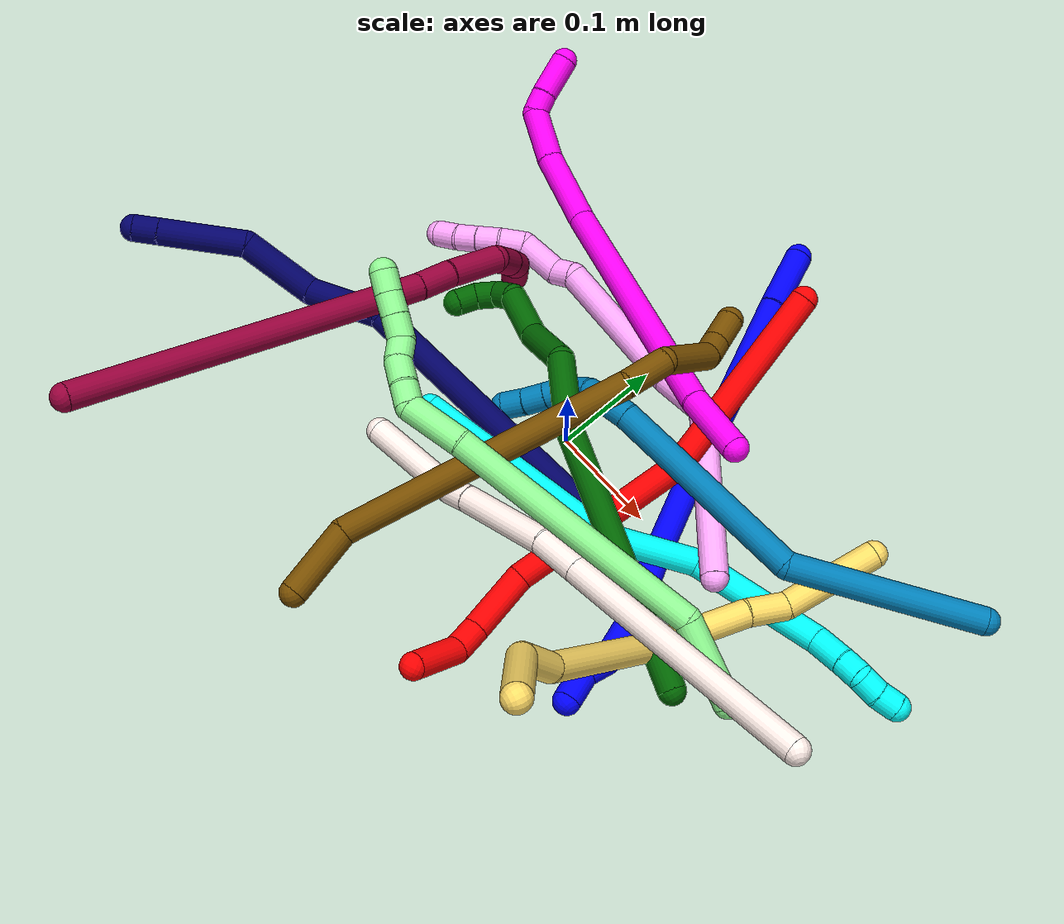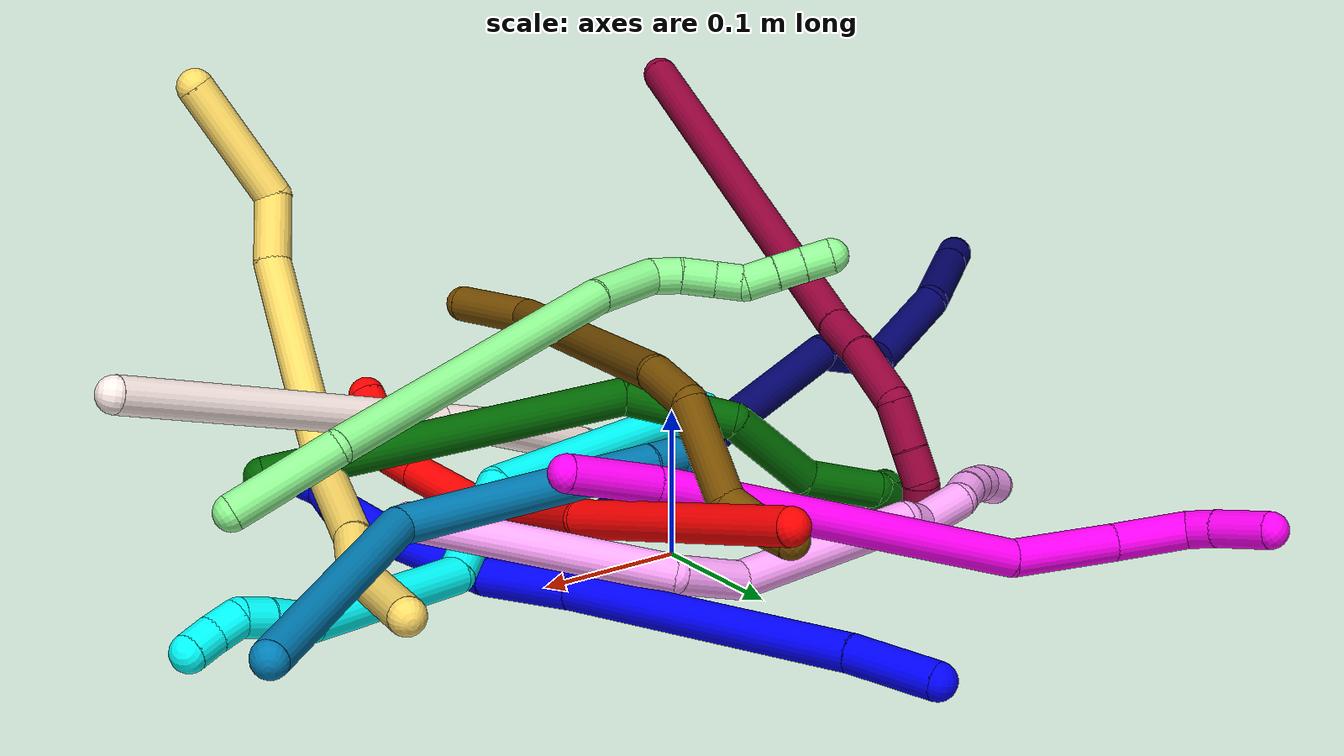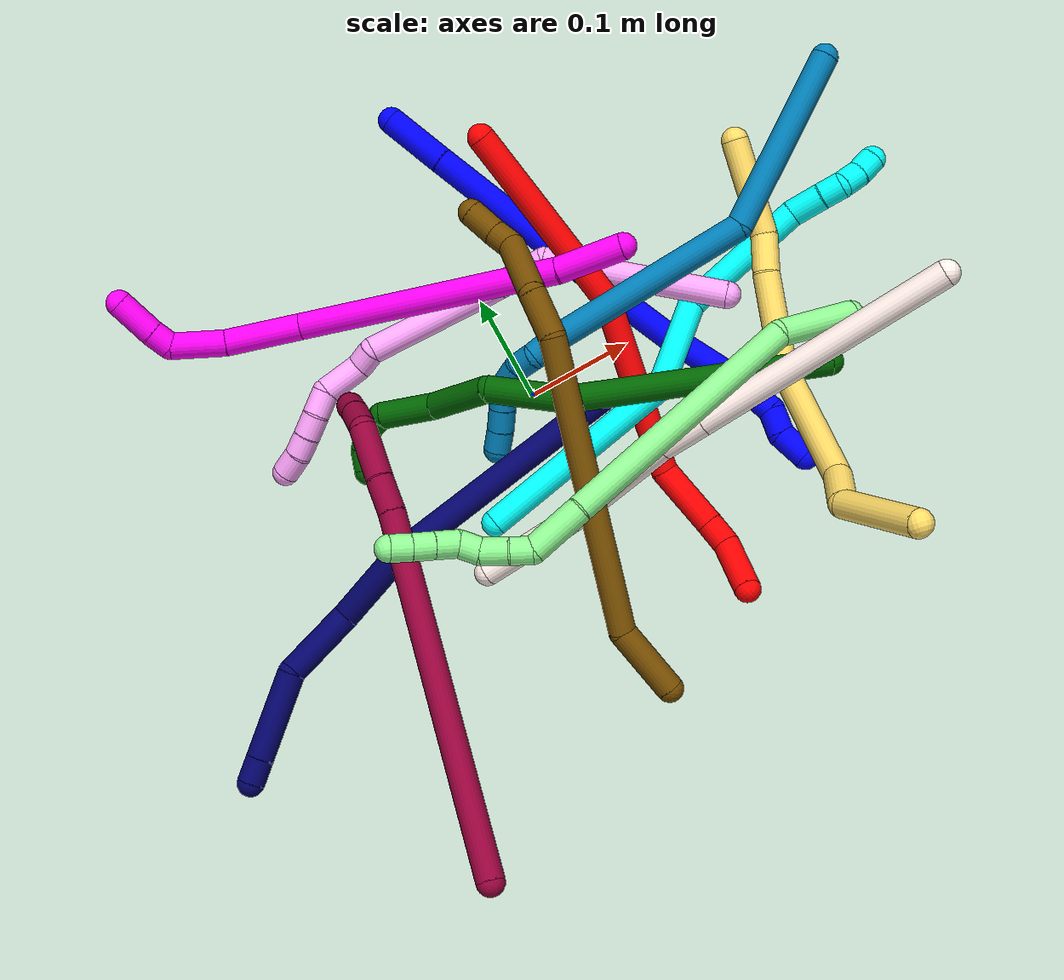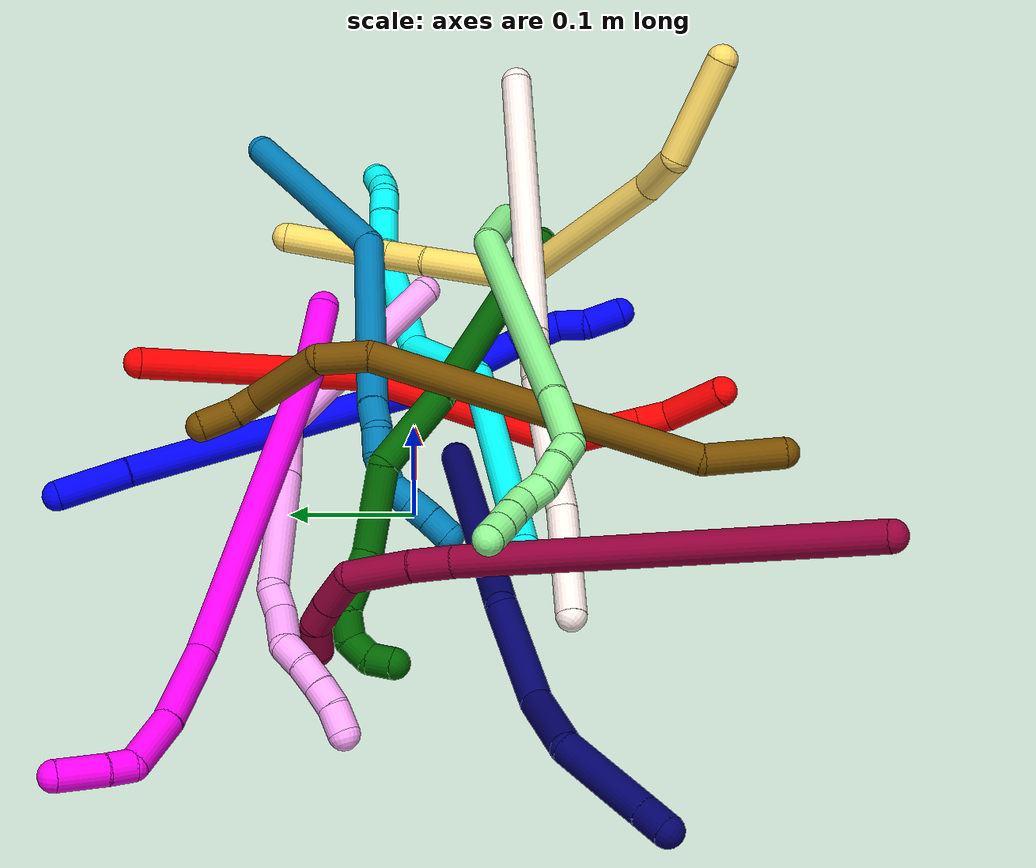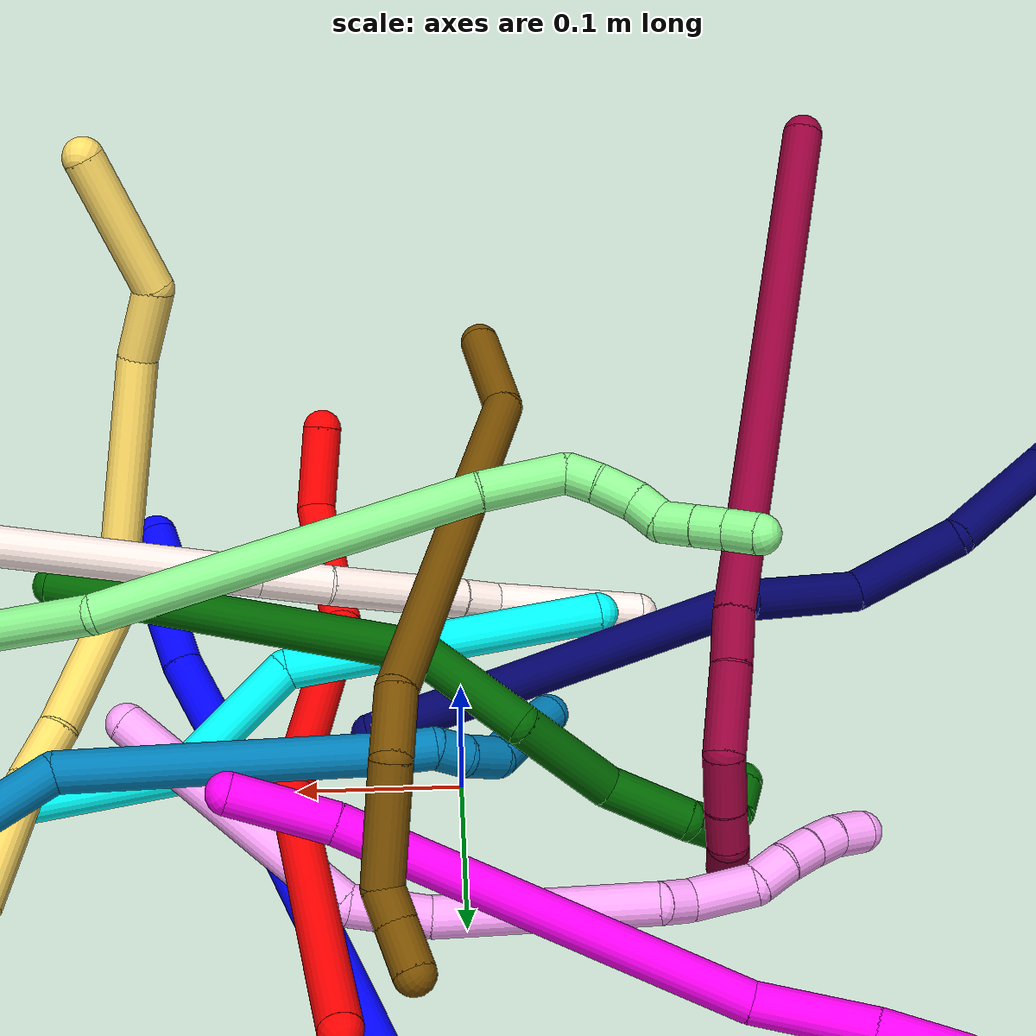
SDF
<sdf version="1.7">
 <world name="default">
  <plugin name="TubeGeneratorPlugin" filename="libtube_generator_plugin.so"/>
  <model name="photoneo_s_sensor">
   <static>1</static>
   <pose>0 0 2 1.57079 1.57079 3.14159</pose>
   <link name="link">
    <inertial><mass>0.1</mass></inertial>
    <sensor name="sensor" type="depth">
     <update_rate>30</update_rate>
     <camera>
      <horizontal_fov>1.22</horizontal_fov>
      <image><width>1920</width><height>1200</height><format>B8G8R8</format></image>
      <clip><near>0.1</near><far>4</far></clip>
      <depth_camera><output>points</output></depth_camera>
     </camera>
     <plugin name="camera_plugin" filename="libgazebo_ros_depth_camera.so">
      <baseline>0.2</baseline>
      <alwaysOn>1</alwaysOn>
      <updateRate>0.0</updateRate>
      <cameraName>camera_ir</cameraName>
      <imageTopicName>/camera/color/image_raw</imageTopicName>
      <cameraInfoTopicName>/camera/color/camera_info</cameraInfoTopicName>
      <depthImageTopicName>/camera/depth/image_raw</depthImageTopicName>
      <depthImageCameraInfoTopicName>/camera/depth/camera_info</depthImageCameraInfoTopicName>
      <pointCloudTopicName>/camera/depth/points</pointCloudTopicName>
      <frameName>fr_optical</frameName>
      <pointCloudCutoff>0.1</pointCloudCutoff>
      <pointCloudCutoffMax>2.0</pointCloudCutoffMax>
      <distortionK1>0</distortionK1>
      <distortionK2>0</distortionK2>
      <distortionK3>0</distortionK3>
      <distortionT1>0</distortionT1>
      <distortionT2>0</distortionT2>
      <CxPrime>0</CxPrime>
      <Cx>0</Cx>
      <Cy>0</Cy>
      <focalLength>0</focalLength>
      <hackBaseline>0</hackBaseline>
     </plugin>
    </sensor>
   </link>
  </model>
  <gravity>0 0 -9.8</gravity>
  <magnetic_field>6e-06 2.3e-05 -4.2e-05</magnetic_field>
  <atmosphere type="adiabatic"/>
  <physics name="default_physics" default="0" type="ode">
   <max_step_size>0.003</max_step_size>
   <real_time_factor>1</real_time_factor>
   <real_time_update_rate>1000</real_time_update_rate>
   <max_contacts>10000</max_contacts>
   <ode>
    <solver>
     <type>quick</type>
     <iters>100</iters>
     <sor>1.3</sor>
     <use_dynamic_moi_rescaling>0</use_dynamic_moi_rescaling>
    </solver>
    <constraints>
     <contact_max_correcting_vel>0</contact_max_correcting_vel>
     <contact_surface_layer>0.001</contact_surface_layer>
     <cfm>0</cfm>
     <erp>0.2</erp>
    </constraints>
   </ode>
  </physics>
  <scene><ambient>0.4 0.4 0.4 1</ambient><background>0.7 0.7 0.7 1</background><shadows>0</shadows></scene>
  <audio><device>default</device></audio>
  <spherical_coordinates>
   <surface_model>EARTH_WGS84</surface_model>
   <latitude_deg>0</latitude_deg>
   <longitude_deg>0</longitude_deg>
   <elevation>0</elevation>
   <heading_deg>0</heading_deg>
  </spherical_coordinates>
  <model name="bin">
   <static>1</static>
   <link name="bottom">
    <collision name="collision-bottom">
     <pose>0 0 -0.01 0 -0 0</pose>
     <geometry><box><size>0.8 0.6 0.02</size></box></geometry>
     <surface>
      <friction><ode><mu>100</mu><mu2>100</mu2></ode></friction>
      <contact><collide_bitmask>65535</collide_bitmask></contact>
     </surface>
    </collision>
   </link>
   <link name="west_wall">
    <collision name="collision-west_wall">
     <pose>-0.41 0 0.1 0 -0 0</pose>
     <geometry><box><size>0.02 0.6 0.2</size></box></geometry>
     <surface>
      <friction><ode><mu>100</mu><mu2>100</mu2></ode></friction>
      <contact><collide_bitmask>65535</collide_bitmask></contact>
     </surface>
    </collision>
   </link>
   <link name="east_wall">
    <collision name="collision-east_wall">
     <pose>0.41 0 0.1 0 -0 0</pose>
     <geometry><box><size>0.02 0.6 0.2</size></box></geometry>
     <surface>
      <friction><ode><mu>100</mu><mu2>100</mu2></ode></friction>
      <contact><collide_bitmask>65535</collide_bitmask></contact>
     </surface>
    </collision>
   </link>
   <link name="south_wall">
    <collision name="collision-south_wall">
     <pose>0 -0.31 0.1 0 -0 0</pose>
     <geometry><box><size>0.8 0.02 0.2</size></box></geometry>
     <surface>
      <friction><ode><mu>100</mu><mu2>100</mu2></ode></friction>
      <contact><collide_bitmask>65535</collide_bitmask></contact>
     </surface>
    </collision>
   </link>
   <link name="north_wall">
    <collision name="collision-north_wall">
     <pose>0 0.31 0.1 0 -0 0</pose>
     <geometry><box><size>0.8 0.02 0.2</size></box></geometry>
     <surface>
      <friction><ode><mu>100</mu><mu2>100</mu2></ode></friction>
      <contact><collide_bitmask>65535</collide_bitmask></contact>
     </surface>
    </collision>
   </link>
  </model>
  <model name="1">
   <static>0</static>
   <link name="1">
    <collision name="collision-cylinder-e_1_1_4">
     <pose>0.006133 -0.024635 0.015986 0.995188 0.205876 0.112108</pose>
     <geometry><cylinder><radius>0.0125</radius><length>0.060001</length></cylinder></geometry>
     <surface>
      <friction><ode><mu>1.16</mu><mu2>1.16</mu2><slip1>0</slip1><slip2>0</slip2></ode></friction>
      <contact><ode><kp>1e+06</kp><kd>1</kd><max_vel>0</max_vel><min_depth>0.001</min_depth></ode></contact>
     </surface>
    </collision>
    <visual name="visual-cylinder-e_1_1_4">
     <pose>0.006133 -0.024635 0.015986 0.995188 0.205876 0.112108</pose>
     <geometry><cylinder><radius>0.0125</radius><length>0.060001</length></cylinder></geometry>
     <material><ambient>0 0 1 1</ambient></material>
    </visual>
    <collision name="collision-cylinder-e_2_4_5">
     <pose>0.041256 -0.129499 0.086183 0.976568 0.290909 0.155313</pose>
     <geometry><cylinder><radius>0.0125</radius><length>0.20215</length></cylinder></geometry>
     <surface>
      <friction><ode><mu>1.16</mu><mu2>1.16</mu2><slip1>0</slip1><slip2>0</slip2></ode></friction>
      <contact><ode><kp>1e+06</kp><kd>1</kd><max_vel>0</max_vel><min_depth>0.001</min_depth></ode></contact>
     </surface>
    </collision>
    <visual name="visual-cylinder-e_2_4_5">
     <pose>0.041256 -0.129499 0.086183 0.976568 0.290909 0.155313</pose>
     <geometry><cylinder><radius>0.0125</radius><length>0.20215</length></cylinder></geometry>
     <material><ambient>0 0 1 1</ambient></material>
    </visual>
    <collision name="collision-cylinder-e_3_5_6">
     <pose>0.081015 -0.234922 0.158413 0.949907 0.334585 0.173237</pose>
     <geometry><cylinder><radius>0.0125</radius><length>0.065584</length></cylinder></geometry>
     <surface>
      <friction><ode><mu>1.16</mu><mu2>1.16</mu2><slip1>0</slip1><slip2>0</slip2></ode></friction>
      <contact><ode><kp>1e+06</kp><kd>1</kd><max_vel>0</max_vel><min_depth>0.001</min_depth></ode></contact>
     </surface>
    </collision>
    <visual name="visual-cylinder-e_3_5_6">
     <pose>0.081015 -0.234922 0.158413 0.949907 0.334585 0.173237</pose>
     <geometry><cylinder><radius>0.0125</radius><length>0.065584</length></cylinder></geometry>
     <material><ambient>0 0 1 1</ambient></material>
    </visual>
    <collision name="collision-cylinder-e_4_6_7">
     <pose>0.094633 -0.289537 0.199817 0.899228 0.075684 0.036537</pose>
     <geometry><cylinder><radius>0.0125</radius><length>0.075382</length></cylinder></geometry>
     <surface>
      <friction><ode><mu>1.16</mu><mu2>1.16</mu2><slip1>0</slip1><slip2>0</slip2></ode></friction>
      <contact><ode><kp>1e+06</kp><kd>1</kd><max_vel>0</max_vel><min_depth>0.001</min_depth></ode></contact>
     </surface>
    </collision>
    <visual name="visual-cylinder-e_4_6_7">
     <pose>0.094633 -0.289537 0.199817 0.899228 0.075684 0.036537</pose>
     <geometry><cylinder><radius>0.0125</radius><length>0.075382</length></cylinder></geometry>
     <material><ambient>0 0 1 1</ambient></material>
    </visual>
    <collision name="collision-cylinder-e_5_7_8">
     <pose>0.098168 -0.337551 0.233991 1.04496 0.031843 0.018338</pose>
     <geometry><cylinder><radius>0.0125</radius><length>0.043015</length></cylinder></geometry>
     <surface>
      <friction><ode><mu>1.16</mu><mu2>1.16</mu2><slip1>0</slip1><slip2>0</slip2></ode></friction>
      <contact><ode><kp>1e+06</kp><kd>1</kd><max_vel>0</max_vel><min_depth>0.001</min_depth></ode></contact>
     </surface>
    </collision>
    <visual name="visual-cylinder-e_5_7_8">
     <pose>0.098168 -0.337551 0.233991 1.04496 0.031843 0.018338</pose>
     <geometry><cylinder><radius>0.0125</radius><length>0.043015</length></cylinder></geometry>
     <material><ambient>0 0 1 1</ambient></material>
    </visual>
    <collision name="collision-cylinder-e_6_8_9">
     <pose>0.099388 -0.368063 0.245293 1.52793 0.04485 0.042968</pose>
     <geometry><cylinder><radius>0.0125</radius><length>0.023886</length></cylinder></geometry>
     <surface>
      <friction><ode><mu>1.16</mu><mu2>1.16</mu2><slip1>0</slip1><slip2>0</slip2></ode></friction>
      <contact><ode><kp>1e+06</kp><kd>1</kd><max_vel>0</max_vel><min_depth>0.001</min_depth></ode></contact>
     </surface>
    </collision>
    <visual name="visual-cylinder-e_6_8_9">
     <pose>0.099388 -0.368063 0.245293 1.52793 0.04485 0.042968</pose>
     <geometry><cylinder><radius>0.0125</radius><length>0.023886</length></cylinder></geometry>
     <material><ambient>0 0 1 1</ambient></material>
    </visual>
    <collision name="collision-cylinder-e_7_9_2">
     <pose>0.10153 -0.392963 0.253132 1.05685 0.107335 0.062702</pose>
     <geometry><cylinder><radius>0.0125</radius><length>0.029982</length></cylinder></geometry>
     <surface>
      <friction><ode><mu>1.16</mu><mu2>1.16</mu2><slip1>0</slip1><slip2>0</slip2></ode></friction>
      <contact><ode><kp>1e+06</kp><kd>1</kd><max_vel>0</max_vel><min_depth>0.001</min_depth></ode></contact>
     </surface>
    </collision>
    <visual name="visual-cylinder-e_7_9_2">
     <pose>0.10153 -0.392963 0.253132 1.05685 0.107335 0.062702</pose>
     <geometry><cylinder><radius>0.0125</radius><length>0.029982</length></cylinder></geometry>
     <material><ambient>0 0 1 1</ambient></material>
    </visual>
    <collision name="collision-sphere-2">
     <pose>0.103136 -0.405942 0.260459 0 -0 0</pose>
     <geometry><sphere><radius>0.0125</radius></sphere></geometry>
     <surface>
      <friction><ode><mu>1.16</mu><mu2>1.16</mu2><slip1>0</slip1><slip2>0</slip2></ode></friction>
      <contact><ode><kp>1e+06</kp><kd>1</kd><max_vel>0</max_vel><min_depth>0.001</min_depth></ode></contact>
     </surface>
    </collision>
    <visual name="visual-sphere-2">
     <pose>0.103136 -0.405942 0.260459 0 -0 0</pose>
     <geometry><sphere><radius>0.0125</radius></sphere></geometry>
     <material><ambient>0 0 1 1</ambient></material>
    </visual>
    <collision name="collision-sphere-9">
     <pose>0.099924 -0.379983 0.245804 0 -0 0</pose>
     <geometry><sphere><radius>0.0125</radius></sphere></geometry>
     <surface>
      <friction><ode><mu>1.16</mu><mu2>1.16</mu2><slip1>0</slip1><slip2>0</slip2></ode></friction>
      <contact><ode><kp>1e+06</kp><kd>1</kd><max_vel>0</max_vel><min_depth>0.001</min_depth></ode></contact>
     </surface>
    </collision>
    <visual name="visual-sphere-9">
     <pose>0.099924 -0.379983 0.245804 0 -0 0</pose>
     <geometry><sphere><radius>0.0125</radius></sphere></geometry>
     <material><ambient>0 0 1 1</ambient></material>
    </visual>
    <collision name="collision-sphere-4">
     <pose>0.012266 -0.049269 0.031971 0 -0 0</pose>
     <geometry><sphere><radius>0.0125</radius></sphere></geometry>
     <surface>
      <friction><ode><mu>1.16</mu><mu2>1.16</mu2><slip1>0</slip1><slip2>0</slip2></ode></friction>
      <contact><ode><kp>1e+06</kp><kd>1</kd><max_vel>0</max_vel><min_depth>0.001</min_depth></ode></contact>
     </surface>
    </collision>
    <visual name="visual-sphere-4">
     <pose>0.012266 -0.049269 0.031971 0 -0 0</pose>
     <geometry><sphere><radius>0.0125</radius></sphere></geometry>
     <material><ambient>0 0 1 1</ambient></material>
    </visual>
    <collision name="collision-sphere-1">
     <geometry><sphere><radius>0.0125</radius></sphere></geometry>
     <surface>
      <friction><ode><mu>1.16</mu><mu2>1.16</mu2><slip1>0</slip1><slip2>0</slip2></ode></friction>
      <contact><ode><kp>1e+06</kp><kd>1</kd><max_vel>0</max_vel><min_depth>0.001</min_depth></ode></contact>
     </surface>
    </collision>
    <visual name="visual-sphere-1">
     <geometry><sphere><radius>0.0125</radius></sphere></geometry>
     <material><ambient>0 0 1 1</ambient></material>
    </visual>
    <collision name="collision-sphere-8">
     <pose>0.098853 -0.356144 0.244781 0 -0 0</pose>
     <geometry><sphere><radius>0.0125</radius></sphere></geometry>
     <surface>
      <friction><ode><mu>1.16</mu><mu2>1.16</mu2><slip1>0</slip1><slip2>0</slip2></ode></friction>
      <contact><ode><kp>1e+06</kp><kd>1</kd><max_vel>0</max_vel><min_depth>0.001</min_depth></ode></contact>
     </surface>
    </collision>
    <visual name="visual-sphere-8">
     <pose>0.098853 -0.356144 0.244781 0 -0 0</pose>
     <geometry><sphere><radius>0.0125</radius></sphere></geometry>
     <material><ambient>0 0 1 1</ambient></material>
    </visual>
    <collision name="collision-sphere-5">
     <pose>0.070247 -0.209729 0.140394 0 -0 0</pose>
     <geometry><sphere><radius>0.0125</radius></sphere></geometry>
     <surface>
      <friction><ode><mu>1.16</mu><mu2>1.16</mu2><slip1>0</slip1><slip2>0</slip2></ode></friction>
      <contact><ode><kp>1e+06</kp><kd>1</kd><max_vel>0</max_vel><min_depth>0.001</min_depth></ode></contact>
     </surface>
    </collision>
    <visual name="visual-sphere-5">
     <pose>0.070247 -0.209729 0.140394 0 -0 0</pose>
     <geometry><sphere><radius>0.0125</radius></sphere></geometry>
     <material><ambient>0 0 1 1</ambient></material>
    </visual>
    <collision name="collision-sphere-6">
     <pose>0.091783 -0.260115 0.176432 0 -0 0</pose>
     <geometry><sphere><radius>0.0125</radius></sphere></geometry>
     <surface>
      <friction><ode><mu>1.16</mu><mu2>1.16</mu2><slip1>0</slip1><slip2>0</slip2></ode></friction>
      <contact><ode><kp>1e+06</kp><kd>1</kd><max_vel>0</max_vel><min_depth>0.001</min_depth></ode></contact>
     </surface>
    </collision>
    <visual name="visual-sphere-6">
     <pose>0.091783 -0.260115 0.176432 0 -0 0</pose>
     <geometry><sphere><radius>0.0125</radius></sphere></geometry>
     <material><ambient>0 0 1 1</ambient></material>
    </visual>
    <collision name="collision-sphere-7">
     <pose>0.097483 -0.318958 0.223201 0 -0 0</pose>
     <geometry><sphere><radius>0.0125</radius></sphere></geometry>
     <surface>
      <friction><ode><mu>1.16</mu><mu2>1.16</mu2><slip1>0</slip1><slip2>0</slip2></ode></friction>
      <contact><ode><kp>1e+06</kp><kd>1</kd><max_vel>0</max_vel><min_depth>0.001</min_depth></ode></contact>
     </surface>
    </collision>
    <visual name="visual-sphere-7">
     <pose>0.097483 -0.318958 0.223201 0 -0 0</pose>
     <geometry><sphere><radius>0.0125</radius></sphere></geometry>
     <material><ambient>0 0 1 1</ambient></material>
    </visual>
    <inertial>
     <pose>0.061591 -0.199965 0.134693 0 -0 0</pose>
     <mass>0.5</mass>
     <inertia>
      <ixx>0.000875</ixx>
      <ixy>0</ixy>
      <ixz>0</ixz>
      <iyy>0.000548</iyy>
      <iyz>0</iyz>
      <izz>0.000436</izz>
     </inertia>
    </inertial>
   </link>
   <pose>0.00945 0.287372 0.011674 -0.946722 1.28713 -1.14363</pose>
  </model>
  <model name="2">
   <static>0</static>
   <link name="2">
    <collision name="collision-cylinder-e_1_1_4">
     <pose>-0.000107 -0.020913 -0.090584 2.9147 -0.001153 -0.010115</pose>
     <geometry><cylinder><radius>0.0125</radius><length>0.185933</length></cylinder></geometry>
     <surface>
      <friction><ode><mu>1.16</mu><mu2>1.16</mu2><slip1>0</slip1><slip2>0</slip2></ode></friction>
      <contact><ode><kp>1e+06</kp><kd>1</kd><max_vel>0</max_vel><min_depth>0.001</min_depth></ode></contact>
     </surface>
    </collision>
    <visual name="visual-cylinder-e_1_1_4">
     <pose>-0.000107 -0.020913 -0.090584 2.9147 -0.001153 -0.010115</pose>
     <geometry><cylinder><radius>0.0125</radius><length>0.185933</length></cylinder></geometry>
     <material><ambient>1 0 0 1</ambient></material>
    </visual>
    <collision name="collision-cylinder-e_2_4_5">
     <pose>-0.023205 -0.075346 -0.256469 2.72279 -0.272009 -1.14422</pose>
     <geometry><cylinder><radius>0.0125</radius><length>0.171144</length></cylinder></geometry>
     <surface>
      <friction><ode><mu>1.16</mu><mu2>1.16</mu2><slip1>0</slip1><slip2>0</slip2></ode></friction>
      <contact><ode><kp>1e+06</kp><kd>1</kd><max_vel>0</max_vel><min_depth>0.001</min_depth></ode></contact>
     </surface>
    </collision>
    <visual name="visual-cylinder-e_2_4_5">
     <pose>-0.023205 -0.075346 -0.256469 2.72279 -0.272009 -1.14422</pose>
     <geometry><cylinder><radius>0.0125</radius><length>0.171144</length></cylinder></geometry>
     <material><ambient>1 0 0 1</ambient></material>
    </visual>
    <collision name="collision-cylinder-e_3_5_6">
     <pose>-0.037327 -0.123117 -0.358846 2.65709 0.28213 1.0432</pose>
     <geometry><cylinder><radius>0.0125</radius><length>0.06371</length></cylinder></geometry>
     <surface>
      <friction><ode><mu>1.16</mu><mu2>1.16</mu2><slip1>0</slip1><slip2>0</slip2></ode></friction>
      <contact><ode><kp>1e+06</kp><kd>1</kd><max_vel>0</max_vel><min_depth>0.001</min_depth></ode></contact>
     </surface>
    </collision>
    <visual name="visual-cylinder-e_3_5_6">
     <pose>-0.037327 -0.123117 -0.358846 2.65709 0.28213 1.0432</pose>
     <geometry><cylinder><radius>0.0125</radius><length>0.06371</length></cylinder></geometry>
     <material><ambient>1 0 0 1</ambient></material>
    </visual>
    <collision name="collision-cylinder-e_4_6_7">
     <pose>-0.024915 -0.143494 -0.396625 2.62174 0.279724 0.973734</pose>
     <geometry><cylinder><radius>0.0125</radius><length>0.025666</length></cylinder></geometry>
     <surface>
      <friction><ode><mu>1.16</mu><mu2>1.16</mu2><slip1>0</slip1><slip2>0</slip2></ode></friction>
      <contact><ode><kp>1e+06</kp><kd>1</kd><max_vel>0</max_vel><min_depth>0.001</min_depth></ode></contact>
     </surface>
    </collision>
    <visual name="visual-cylinder-e_4_6_7">
     <pose>-0.024915 -0.143494 -0.396625 2.62174 0.279724 0.973734</pose>
     <geometry><cylinder><radius>0.0125</radius><length>0.025666</length></cylinder></geometry>
     <material><ambient>1 0 0 1</ambient></material>
    </visual>
    <collision name="collision-cylinder-e_5_7_2">
     <pose>-0.010989 -0.171705 -0.418345 2.03346 0.398249 0.63056</pose>
     <geometry><cylinder><radius>0.0125</radius><length>0.053547</length></cylinder></geometry>
     <surface>
      <friction><ode><mu>1.16</mu><mu2>1.16</mu2><slip1>0</slip1><slip2>0</slip2></ode></friction>
      <contact><ode><kp>1e+06</kp><kd>1</kd><max_vel>0</max_vel><min_depth>0.001</min_depth></ode></contact>
     </surface>
    </collision>
    <visual name="visual-cylinder-e_5_7_2">
     <pose>-0.010989 -0.171705 -0.418345 2.03346 0.398249 0.63056</pose>
     <geometry><cylinder><radius>0.0125</radius><length>0.053547</length></cylinder></geometry>
     <material><ambient>1 0 0 1</ambient></material>
    </visual>
    <collision name="collision-sphere-2">
     <pose>-0.000606 -0.193789 -0.429359 0 -0 0</pose>
     <geometry><sphere><radius>0.0125</radius></sphere></geometry>
     <surface>
      <friction><ode><mu>1.16</mu><mu2>1.16</mu2><slip1>0</slip1><slip2>0</slip2></ode></friction>
      <contact><ode><kp>1e+06</kp><kd>1</kd><max_vel>0</max_vel><min_depth>0.001</min_depth></ode></contact>
     </surface>
    </collision>
    <visual name="visual-sphere-2">
     <pose>-0.000606 -0.193789 -0.429359 0 -0 0</pose>
     <geometry><sphere><radius>0.0125</radius></sphere></geometry>
     <material><ambient>1 0 0 1</ambient></material>
    </visual>
    <collision name="collision-sphere-7">
     <pose>-0.021372 -0.149621 -0.40733 0 -0 0</pose>
     <geometry><sphere><radius>0.0125</radius></sphere></geometry>
     <surface>
      <friction><ode><mu>1.16</mu><mu2>1.16</mu2><slip1>0</slip1><slip2>0</slip2></ode></friction>
      <contact><ode><kp>1e+06</kp><kd>1</kd><max_vel>0</max_vel><min_depth>0.001</min_depth></ode></contact>
     </surface>
    </collision>
    <visual name="visual-sphere-7">
     <pose>-0.021372 -0.149621 -0.40733 0 -0 0</pose>
     <geometry><sphere><radius>0.0125</radius></sphere></geometry>
     <material><ambient>1 0 0 1</ambient></material>
    </visual>
    <collision name="collision-sphere-6">
     <pose>-0.028458 -0.137367 -0.38592 0 -0 0</pose>
     <geometry><sphere><radius>0.0125</radius></sphere></geometry>
     <surface>
      <friction><ode><mu>1.16</mu><mu2>1.16</mu2><slip1>0</slip1><slip2>0</slip2></ode></friction>
      <contact><ode><kp>1e+06</kp><kd>1</kd><max_vel>0</max_vel><min_depth>0.001</min_depth></ode></contact>
     </surface>
    </collision>
    <visual name="visual-sphere-6">
     <pose>-0.028458 -0.137367 -0.38592 0 -0 0</pose>
     <geometry><sphere><radius>0.0125</radius></sphere></geometry>
     <material><ambient>1 0 0 1</ambient></material>
    </visual>
    <collision name="collision-sphere-5">
     <pose>-0.046195 -0.108866 -0.331772 0 -0 0</pose>
     <geometry><sphere><radius>0.0125</radius></sphere></geometry>
     <surface>
      <friction><ode><mu>1.16</mu><mu2>1.16</mu2><slip1>0</slip1><slip2>0</slip2></ode></friction>
      <contact><ode><kp>1e+06</kp><kd>1</kd><max_vel>0</max_vel><min_depth>0.001</min_depth></ode></contact>
     </surface>
    </collision>
    <visual name="visual-sphere-5">
     <pose>-0.046195 -0.108866 -0.331772 0 -0 0</pose>
     <geometry><sphere><radius>0.0125</radius></sphere></geometry>
     <material><ambient>1 0 0 1</ambient></material>
    </visual>
    <collision name="collision-sphere-1">
     <geometry><sphere><radius>0.0125</radius></sphere></geometry>
     <surface>
      <friction><ode><mu>1.16</mu><mu2>1.16</mu2><slip1>0</slip1><slip2>0</slip2></ode></friction>
      <contact><ode><kp>1e+06</kp><kd>1</kd><max_vel>0</max_vel><min_depth>0.001</min_depth></ode></contact>
     </surface>
    </collision>
    <visual name="visual-sphere-1">
     <geometry><sphere><radius>0.0125</radius></sphere></geometry>
     <material><ambient>1 0 0 1</ambient></material>
    </visual>
    <collision name="collision-sphere-4">
     <pose>-0.000214 -0.041827 -0.181167 0 -0 0</pose>
     <geometry><sphere><radius>0.0125</radius></sphere></geometry>
     <surface>
      <friction><ode><mu>1.16</mu><mu2>1.16</mu2><slip1>0</slip1><slip2>0</slip2></ode></friction>
      <contact><ode><kp>1e+06</kp><kd>1</kd><max_vel>0</max_vel><min_depth>0.001</min_depth></ode></contact>
     </surface>
    </collision>
    <visual name="visual-sphere-4">
     <pose>-0.000214 -0.041827 -0.181167 0 -0 0</pose>
     <geometry><sphere><radius>0.0125</radius></sphere></geometry>
     <material><ambient>1 0 0 1</ambient></material>
    </visual>
    <inertial>
     <pose>-0.015194 -0.075009 -0.232357 0 -0 0</pose>
     <mass>0.5</mass>
     <inertia>
      <ixx>0.000388</ixx>
      <ixy>0</ixy>
      <ixz>0</ixz>
      <iyy>-0.001021</iyy>
      <iyz>0</iyz>
      <izz>0.000381</izz>
     </inertia>
    </inertial>
   </link>
   <pose>0.069031 0.219676 0.103029 -1.01887 -0.761992 -0.056826</pose>
  </model>
  <model name="3">
   <static>0</static>
   <link name="3">
    <collision name="collision-cylinder-e_1_1_4">
     <pose>0.067247 0.026626 0.06522 -0.387601 0.762175 -0.156953</pose>
     <geometry><cylinder><radius>0.0125</radius><length>0.194779</length></cylinder></geometry>
     <surface>
      <friction><ode><mu>1.16</mu><mu2>1.16</mu2><slip1>0</slip1><slip2>0</slip2></ode></friction>
      <contact><ode><kp>1e+06</kp><kd>1</kd><max_vel>0</max_vel><min_depth>0.001</min_depth></ode></contact>
     </surface>
    </collision>
    <visual name="visual-cylinder-e_1_1_4">
     <pose>0.067247 0.026626 0.06522 -0.387601 0.762175 -0.156953</pose>
     <geometry><cylinder><radius>0.0125</radius><length>0.194779</length></cylinder></geometry>
     <material><ambient>0.003922 1 0.996078 1</ambient></material>
    </visual>
    <collision name="collision-cylinder-e_2_4_5">
     <pose>0.152015 0.087111 0.152813 -0.986867 0.407554 -0.221362</pose>
     <geometry><cylinder><radius>0.0125</radius><length>0.088407</length></cylinder></geometry>
     <surface>
      <friction><ode><mu>1.16</mu><mu2>1.16</mu2><slip1>0</slip1><slip2>0</slip2></ode></friction>
      <contact><ode><kp>1e+06</kp><kd>1</kd><max_vel>0</max_vel><min_depth>0.001</min_depth></ode></contact>
     </surface>
    </collision>
    <visual name="visual-cylinder-e_2_4_5">
     <pose>0.152015 0.087111 0.152813 -0.986867 0.407554 -0.221362</pose>
     <geometry><cylinder><radius>0.0125</radius><length>0.088407</length></cylinder></geometry>
     <material><ambient>0.003922 1 0.996078 1</ambient></material>
    </visual>
    <collision name="collision-cylinder-e_3_5_6">
     <pose>0.209152 0.137318 0.220303 -0.347661 0.690135 -0.126073</pose>
     <geometry><cylinder><radius>0.0125</radius><length>0.124454</length></cylinder></geometry>
     <surface>
      <friction><ode><mu>1.16</mu><mu2>1.16</mu2><slip1>0</slip1><slip2>0</slip2></ode></friction>
      <contact><ode><kp>1e+06</kp><kd>1</kd><max_vel>0</max_vel><min_depth>0.001</min_depth></ode></contact>
     </surface>
    </collision>
    <visual name="visual-cylinder-e_3_5_6">
     <pose>0.209152 0.137318 0.220303 -0.347661 0.690135 -0.126073</pose>
     <geometry><cylinder><radius>0.0125</radius><length>0.124454</length></cylinder></geometry>
     <material><ambient>0.003922 1 0.996078 1</ambient></material>
    </visual>
    <collision name="collision-cylinder-e_4_6_7">
     <pose>0.258639 0.152165 0.277752 0.121227 0.671313 0.042336</pose>
     <geometry><cylinder><radius>0.0125</radius><length>0.031737</length></cylinder></geometry>
     <surface>
      <friction><ode><mu>1.16</mu><mu2>1.16</mu2><slip1>0</slip1><slip2>0</slip2></ode></friction>
      <contact><ode><kp>1e+06</kp><kd>1</kd><max_vel>0</max_vel><min_depth>0.001</min_depth></ode></contact>
     </surface>
    </collision>
    <visual name="visual-cylinder-e_4_6_7">
     <pose>0.258639 0.152165 0.277752 0.121227 0.671313 0.042336</pose>
     <geometry><cylinder><radius>0.0125</radius><length>0.031737</length></cylinder></geometry>
     <material><ambient>0.003922 1 0.996078 1</ambient></material>
    </visual>
    <collision name="collision-cylinder-e_5_7_8">
     <pose>0.275423 0.150243 0.297522 0.056295 0.748236 0.022107</pose>
     <geometry><cylinder><radius>0.0125</radius><length>0.020324</length></cylinder></geometry>
     <surface>
      <friction><ode><mu>1.16</mu><mu2>1.16</mu2><slip1>0</slip1><slip2>0</slip2></ode></friction>
      <contact><ode><kp>1e+06</kp><kd>1</kd><max_vel>0</max_vel><min_depth>0.001</min_depth></ode></contact>
     </surface>
    </collision>
    <visual name="visual-cylinder-e_5_7_8">
     <pose>0.275423 0.150243 0.297522 0.056295 0.748236 0.022107</pose>
     <geometry><cylinder><radius>0.0125</radius><length>0.020324</length></cylinder></geometry>
     <material><ambient>0.003922 1 0.996078 1</ambient></material>
    </visual>
    <collision name="collision-cylinder-e_6_8_9">
     <pose>0.290436 0.153939 0.309224 -0.767255 0.939043 -0.403984</pose>
     <geometry><cylinder><radius>0.0125</radius><length>0.020073</length></cylinder></geometry>
     <surface>
      <friction><ode><mu>1.16</mu><mu2>1.16</mu2><slip1>0</slip1><slip2>0</slip2></ode></friction>
      <contact><ode><kp>1e+06</kp><kd>1</kd><max_vel>0</max_vel><min_depth>0.001</min_depth></ode></contact>
     </surface>
    </collision>
    <visual name="visual-cylinder-e_6_8_9">
     <pose>0.290436 0.153939 0.309224 -0.767255 0.939043 -0.403984</pose>
     <geometry><cylinder><radius>0.0125</radius><length>0.020073</length></cylinder></geometry>
     <material><ambient>0.003922 1 0.996078 1</ambient></material>
    </visual>
    <collision name="collision-cylinder-e_7_9_2">
     <pose>0.30544 0.163079 0.318907 -0.748071 0.751541 -0.307266</pose>
     <geometry><cylinder><radius>0.0125</radius><length>0.020226</length></cylinder></geometry>
     <surface>
      <friction><ode><mu>1.16</mu><mu2>1.16</mu2><slip1>0</slip1><slip2>0</slip2></ode></friction>
      <contact><ode><kp>1e+06</kp><kd>1</kd><max_vel>0</max_vel><min_depth>0.001</min_depth></ode></contact>
     </surface>
    </collision>
    <visual name="visual-cylinder-e_7_9_2">
     <pose>0.30544 0.163079 0.318907 -0.748071 0.751541 -0.307266</pose>
     <geometry><cylinder><radius>0.0125</radius><length>0.020226</length></cylinder></geometry>
     <material><ambient>0.003922 1 0.996078 1</ambient></material>
    </visual>
    <collision name="collision-sphere-2">
     <pose>0.312345 0.168105 0.324323 0 -0 0</pose>
     <geometry><sphere><radius>0.0125</radius></sphere></geometry>
     <surface>
      <friction><ode><mu>1.16</mu><mu2>1.16</mu2><slip1>0</slip1><slip2>0</slip2></ode></friction>
      <contact><ode><kp>1e+06</kp><kd>1</kd><max_vel>0</max_vel><min_depth>0.001</min_depth></ode></contact>
     </surface>
    </collision>
    <visual name="visual-sphere-2">
     <pose>0.312345 0.168105 0.324323 0 -0 0</pose>
     <geometry><sphere><radius>0.0125</radius></sphere></geometry>
     <material><ambient>0.003922 1 0.996078 1</ambient></material>
    </visual>
    <collision name="collision-sphere-9">
     <pose>0.298535 0.158053 0.313491 0 -0 0</pose>
     <geometry><sphere><radius>0.0125</radius></sphere></geometry>
     <surface>
      <friction><ode><mu>1.16</mu><mu2>1.16</mu2><slip1>0</slip1><slip2>0</slip2></ode></friction>
      <contact><ode><kp>1e+06</kp><kd>1</kd><max_vel>0</max_vel><min_depth>0.001</min_depth></ode></contact>
     </surface>
    </collision>
    <visual name="visual-sphere-9">
     <pose>0.298535 0.158053 0.313491 0 -0 0</pose>
     <geometry><sphere><radius>0.0125</radius></sphere></geometry>
     <material><ambient>0.003922 1 0.996078 1</ambient></material>
    </visual>
    <collision name="collision-sphere-4">
     <pose>0.134494 0.053252 0.130439 0 -0 0</pose>
     <geometry><sphere><radius>0.0125</radius></sphere></geometry>
     <surface>
      <friction><ode><mu>1.16</mu><mu2>1.16</mu2><slip1>0</slip1><slip2>0</slip2></ode></friction>
      <contact><ode><kp>1e+06</kp><kd>1</kd><max_vel>0</max_vel><min_depth>0.001</min_depth></ode></contact>
     </surface>
    </collision>
    <visual name="visual-sphere-4">
     <pose>0.134494 0.053252 0.130439 0 -0 0</pose>
     <geometry><sphere><radius>0.0125</radius></sphere></geometry>
     <material><ambient>0.003922 1 0.996078 1</ambient></material>
    </visual>
    <collision name="collision-sphere-1">
     <geometry><sphere><radius>0.0125</radius></sphere></geometry>
     <surface>
      <friction><ode><mu>1.16</mu><mu2>1.16</mu2><slip1>0</slip1><slip2>0</slip2></ode></friction>
      <contact><ode><kp>1e+06</kp><kd>1</kd><max_vel>0</max_vel><min_depth>0.001</min_depth></ode></contact>
     </surface>
    </collision>
    <visual name="visual-sphere-1">
     <geometry><sphere><radius>0.0125</radius></sphere></geometry>
     <material><ambient>0.003922 1 0.996078 1</ambient></material>
    </visual>
    <collision name="collision-sphere-8">
     <pose>0.282337 0.149824 0.304958 0 -0 0</pose>
     <geometry><sphere><radius>0.0125</radius></sphere></geometry>
     <surface>
      <friction><ode><mu>1.16</mu><mu2>1.16</mu2><slip1>0</slip1><slip2>0</slip2></ode></friction>
      <contact><ode><kp>1e+06</kp><kd>1</kd><max_vel>0</max_vel><min_depth>0.001</min_depth></ode></contact>
     </surface>
    </collision>
    <visual name="visual-sphere-8">
     <pose>0.282337 0.149824 0.304958 0 -0 0</pose>
     <geometry><sphere><radius>0.0125</radius></sphere></geometry>
     <material><ambient>0.003922 1 0.996078 1</ambient></material>
    </visual>
    <collision name="collision-sphere-5">
     <pose>0.169536 0.120969 0.175187 0 -0 0</pose>
     <geometry><sphere><radius>0.0125</radius></sphere></geometry>
     <surface>
      <friction><ode><mu>1.16</mu><mu2>1.16</mu2><slip1>0</slip1><slip2>0</slip2></ode></friction>
      <contact><ode><kp>1e+06</kp><kd>1</kd><max_vel>0</max_vel><min_depth>0.001</min_depth></ode></contact>
     </surface>
    </collision>
    <visual name="visual-sphere-5">
     <pose>0.169536 0.120969 0.175187 0 -0 0</pose>
     <geometry><sphere><radius>0.0125</radius></sphere></geometry>
     <material><ambient>0.003922 1 0.996078 1</ambient></material>
    </visual>
    <collision name="collision-sphere-6">
     <pose>0.248768 0.153668 0.265418 0 -0 0</pose>
     <geometry><sphere><radius>0.0125</radius></sphere></geometry>
     <surface>
      <friction><ode><mu>1.16</mu><mu2>1.16</mu2><slip1>0</slip1><slip2>0</slip2></ode></friction>
      <contact><ode><kp>1e+06</kp><kd>1</kd><max_vel>0</max_vel><min_depth>0.001</min_depth></ode></contact>
     </surface>
    </collision>
    <visual name="visual-sphere-6">
     <pose>0.248768 0.153668 0.265418 0 -0 0</pose>
     <geometry><sphere><radius>0.0125</radius></sphere></geometry>
     <material><ambient>0.003922 1 0.996078 1</ambient></material>
    </visual>
    <collision name="collision-sphere-7">
     <pose>0.268509 0.150662 0.290086 0 -0 0</pose>
     <geometry><sphere><radius>0.0125</radius></sphere></geometry>
     <surface>
      <friction><ode><mu>1.16</mu><mu2>1.16</mu2><slip1>0</slip1><slip2>0</slip2></ode></friction>
      <contact><ode><kp>1e+06</kp><kd>1</kd><max_vel>0</max_vel><min_depth>0.001</min_depth></ode></contact>
     </surface>
    </collision>
    <visual name="visual-sphere-7">
     <pose>0.268509 0.150662 0.290086 0 -0 0</pose>
     <geometry><sphere><radius>0.0125</radius></sphere></geometry>
     <material><ambient>0.003922 1 0.996078 1</ambient></material>
    </visual>
    <inertial>
     <pose>0.156762 0.088497 0.1623 0 -0 0</pose>
     <mass>0.5</mass>
     <inertia>
      <ixx>0.000558</ixx>
      <ixy>0</ixy>
      <ixz>0</ixz>
      <iyy>0.000713</iyy>
      <iyz>0</iyz>
      <izz>-0.000802</izz>
     </inertia>
    </inertial>
   </link>
   <pose>-0.08728 -0.085244 0.059307 -0.835069 0.362016 -0.569411</pose>
  </model>
  <model name="4">
   <static>0</static>
   <link name="4">
    <collision name="collision-cylinder-e_1_1_4">
     <pose>0.020566 -0.071524 0.042304 1.03668 0.242614 0.138837</pose>
     <geometry><cylinder><radius>0.0125</radius><length>0.171211</length></cylinder></geometry>
     <surface>
      <friction><ode><mu>1.16</mu><mu2>1.16</mu2><slip1>0</slip1><slip2>0</slip2></ode></friction>
      <contact><ode><kp>1e+06</kp><kd>1</kd><max_vel>0</max_vel><min_depth>0.001</min_depth></ode></contact>
     </surface>
    </collision>
    <visual name="visual-cylinder-e_1_1_4">
     <pose>0.020566 -0.071524 0.042304 1.03668 0.242614 0.138837</pose>
     <geometry><cylinder><radius>0.0125</radius><length>0.171211</length></cylinder></geometry>
     <material><ambient>1 0.65098 0.996078 1</ambient></material>
    </visual>
    <collision name="collision-cylinder-e_2_4_5">
     <pose>0.038539 -0.153543 0.107289 0.433327 -0.103378 -0.022775</pose>
     <geometry><cylinder><radius>0.0125</radius><length>0.050251</length></cylinder></geometry>
     <surface>
      <friction><ode><mu>1.16</mu><mu2>1.16</mu2><slip1>0</slip1><slip2>0</slip2></ode></friction>
      <contact><ode><kp>1e+06</kp><kd>1</kd><max_vel>0</max_vel><min_depth>0.001</min_depth></ode></contact>
     </surface>
    </collision>
    <visual name="visual-cylinder-e_2_4_5">
     <pose>0.038539 -0.153543 0.107289 0.433327 -0.103378 -0.022775</pose>
     <geometry><cylinder><radius>0.0125</radius><length>0.050251</length></cylinder></geometry>
     <material><ambient>1 0.65098 0.996078 1</ambient></material>
    </visual>
    <collision name="collision-cylinder-e_3_5_6">
     <pose>0.009601 -0.202887 0.176178 0.699114 -0.411479 -0.151855</pose>
     <geometry><cylinder><radius>0.0125</radius><length>0.131737</length></cylinder></geometry>
     <surface>
      <friction><ode><mu>1.16</mu><mu2>1.16</mu2><slip1>0</slip1><slip2>0</slip2></ode></friction>
      <contact><ode><kp>1e+06</kp><kd>1</kd><max_vel>0</max_vel><min_depth>0.001</min_depth></ode></contact>
     </surface>
    </collision>
    <visual name="visual-cylinder-e_3_5_6">
     <pose>0.009601 -0.202887 0.176178 0.699114 -0.411479 -0.151855</pose>
     <geometry><cylinder><radius>0.0125</radius><length>0.131737</length></cylinder></geometry>
     <material><ambient>1 0.65098 0.996078 1</ambient></material>
    </visual>
    <collision name="collision-cylinder-e_4_6_7">
     <pose>-0.018452 -0.242404 0.232587 0.065193 -0.165573 -0.005411</pose>
     <geometry><cylinder><radius>0.0125</radius><length>0.020727</length></cylinder></geometry>
     <surface>
      <friction><ode><mu>1.16</mu><mu2>1.16</mu2><slip1>0</slip1><slip2>0</slip2></ode></friction>
      <contact><ode><kp>1e+06</kp><kd>1</kd><max_vel>0</max_vel><min_depth>0.001</min_depth></ode></contact>
     </surface>
    </collision>
    <visual name="visual-cylinder-e_4_6_7">
     <pose>-0.018452 -0.242404 0.232587 0.065193 -0.165573 -0.005411</pose>
     <geometry><cylinder><radius>0.0125</radius><length>0.020727</length></cylinder></geometry>
     <material><ambient>1 0.65098 0.996078 1</ambient></material>
    </visual>
    <collision name="collision-cylinder-e_5_7_8">
     <pose>-0.030581 -0.252242 0.256398 0.592988 -0.565674 -0.177109</pose>
     <geometry><cylinder><radius>0.0125</radius><length>0.038884</length></cylinder></geometry>
     <surface>
      <friction><ode><mu>1.16</mu><mu2>1.16</mu2><slip1>0</slip1><slip2>0</slip2></ode></friction>
      <contact><ode><kp>1e+06</kp><kd>1</kd><max_vel>0</max_vel><min_depth>0.001</min_depth></ode></contact>
     </surface>
    </collision>
    <visual name="visual-cylinder-e_5_7_8">
     <pose>-0.030581 -0.252242 0.256398 0.592988 -0.565674 -0.177109</pose>
     <geometry><cylinder><radius>0.0125</radius><length>0.038884</length></cylinder></geometry>
     <material><ambient>1 0.65098 0.996078 1</ambient></material>
    </visual>
    <collision name="collision-cylinder-e_6_8_9">
     <pose>-0.047939 -0.260735 0.279189 -0.073879 -0.645871 0.024734</pose>
     <geometry><cylinder><radius>0.0125</radius><length>0.023055</length></cylinder></geometry>
     <surface>
      <friction><ode><mu>1.16</mu><mu2>1.16</mu2><slip1>0</slip1><slip2>0</slip2></ode></friction>
      <contact><ode><kp>1e+06</kp><kd>1</kd><max_vel>0</max_vel><min_depth>0.001</min_depth></ode></contact>
     </surface>
    </collision>
    <visual name="visual-cylinder-e_6_8_9">
     <pose>-0.047939 -0.260735 0.279189 -0.073879 -0.645871 0.024734</pose>
     <geometry><cylinder><radius>0.0125</radius><length>0.023055</length></cylinder></geometry>
     <material><ambient>1 0.65098 0.996078 1</ambient></material>
    </visual>
    <collision name="collision-cylinder-e_7_9_10">
     <pose>-0.059776 -0.258967 0.297999 -0.11256 -0.468054 0.02686</pose>
     <geometry><cylinder><radius>0.0125</radius><length>0.021717</length></cylinder></geometry>
     <surface>
      <friction><ode><mu>1.16</mu><mu2>1.16</mu2><slip1>0</slip1><slip2>0</slip2></ode></friction>
      <contact><ode><kp>1e+06</kp><kd>1</kd><max_vel>0</max_vel><min_depth>0.001</min_depth></ode></contact>
     </surface>
    </collision>
    <visual name="visual-cylinder-e_7_9_10">
     <pose>-0.059776 -0.258967 0.297999 -0.11256 -0.468054 0.02686</pose>
     <geometry><cylinder><radius>0.0125</radius><length>0.021717</length></cylinder></geometry>
     <material><ambient>1 0.65098 0.996078 1</ambient></material>
    </visual>
    <collision name="collision-cylinder-e_8_10_11">
     <pose>-0.068603 -0.257053 0.316859 -0.089147 -0.400895 0.018124</pose>
     <geometry><cylinder><radius>0.0125</radius><length>0.020132</length></cylinder></geometry>
     <surface>
      <friction><ode><mu>1.16</mu><mu2>1.16</mu2><slip1>0</slip1><slip2>0</slip2></ode></friction>
      <contact><ode><kp>1e+06</kp><kd>1</kd><max_vel>0</max_vel><min_depth>0.001</min_depth></ode></contact>
     </surface>
    </collision>
    <visual name="visual-cylinder-e_8_10_11">
     <pose>-0.068603 -0.257053 0.316859 -0.089147 -0.400895 0.018124</pose>
     <geometry><cylinder><radius>0.0125</radius><length>0.020132</length></cylinder></geometry>
     <material><ambient>1 0.65098 0.996078 1</ambient></material>
    </visual>
    <collision name="collision-cylinder-e_9_11_2">
     <pose>-0.075013 -0.25656 0.336949 0.030516 -0.224602 -0.003442</pose>
     <geometry><cylinder><radius>0.0125</radius><length>0.022288</length></cylinder></geometry>
     <surface>
      <friction><ode><mu>1.16</mu><mu2>1.16</mu2><slip1>0</slip1><slip2>0</slip2></ode></friction>
      <contact><ode><kp>1e+06</kp><kd>1</kd><max_vel>0</max_vel><min_depth>0.001</min_depth></ode></contact>
     </surface>
    </collision>
    <visual name="visual-cylinder-e_9_11_2">
     <pose>-0.075013 -0.25656 0.336949 0.030516 -0.224602 -0.003442</pose>
     <geometry><cylinder><radius>0.0125</radius><length>0.022288</length></cylinder></geometry>
     <material><ambient>1 0.65098 0.996078 1</ambient></material>
    </visual>
    <collision name="collision-sphere-2">
     <pose>-0.077495 -0.256891 0.347808 0 -0 0</pose>
     <geometry><sphere><radius>0.0125</radius></sphere></geometry>
     <surface>
      <friction><ode><mu>1.16</mu><mu2>1.16</mu2><slip1>0</slip1><slip2>0</slip2></ode></friction>
      <contact><ode><kp>1e+06</kp><kd>1</kd><max_vel>0</max_vel><min_depth>0.001</min_depth></ode></contact>
     </surface>
    </collision>
    <visual name="visual-sphere-2">
     <pose>-0.077495 -0.256891 0.347808 0 -0 0</pose>
     <geometry><sphere><radius>0.0125</radius></sphere></geometry>
     <material><ambient>1 0.65098 0.996078 1</ambient></material>
    </visual>
    <collision name="collision-sphere-11">
     <pose>-0.072531 -0.256228 0.32609 0 -0 0</pose>
     <geometry><sphere><radius>0.0125</radius></sphere></geometry>
     <surface>
      <friction><ode><mu>1.16</mu><mu2>1.16</mu2><slip1>0</slip1><slip2>0</slip2></ode></friction>
      <contact><ode><kp>1e+06</kp><kd>1</kd><max_vel>0</max_vel><min_depth>0.001</min_depth></ode></contact>
     </surface>
    </collision>
    <visual name="visual-sphere-11">
     <pose>-0.072531 -0.256228 0.32609 0 -0 0</pose>
     <geometry><sphere><radius>0.0125</radius></sphere></geometry>
     <material><ambient>1 0.65098 0.996078 1</ambient></material>
    </visual>
    <collision name="collision-sphere-10">
     <pose>-0.064675 -0.257878 0.307628 0 -0 0</pose>
     <geometry><sphere><radius>0.0125</radius></sphere></geometry>
     <surface>
      <friction><ode><mu>1.16</mu><mu2>1.16</mu2><slip1>0</slip1><slip2>0</slip2></ode></friction>
      <contact><ode><kp>1e+06</kp><kd>1</kd><max_vel>0</max_vel><min_depth>0.001</min_depth></ode></contact>
     </surface>
    </collision>
    <visual name="visual-sphere-10">
     <pose>-0.064675 -0.257878 0.307628 0 -0 0</pose>
     <geometry><sphere><radius>0.0125</radius></sphere></geometry>
     <material><ambient>1 0.65098 0.996078 1</ambient></material>
    </visual>
    <collision name="collision-sphere-9">
     <pose>-0.054878 -0.260055 0.28837 0 -0 0</pose>
     <geometry><sphere><radius>0.0125</radius></sphere></geometry>
     <surface>
      <friction><ode><mu>1.16</mu><mu2>1.16</mu2><slip1>0</slip1><slip2>0</slip2></ode></friction>
      <contact><ode><kp>1e+06</kp><kd>1</kd><max_vel>0</max_vel><min_depth>0.001</min_depth></ode></contact>
     </surface>
    </collision>
    <visual name="visual-sphere-9">
     <pose>-0.054878 -0.260055 0.28837 0 -0 0</pose>
     <geometry><sphere><radius>0.0125</radius></sphere></geometry>
     <material><ambient>1 0.65098 0.996078 1</ambient></material>
    </visual>
    <collision name="collision-sphere-4">
     <pose>0.041132 -0.143049 0.084607 0 -0 0</pose>
     <geometry><sphere><radius>0.0125</radius></sphere></geometry>
     <surface>
      <friction><ode><mu>1.16</mu><mu2>1.16</mu2><slip1>0</slip1><slip2>0</slip2></ode></friction>
      <contact><ode><kp>1e+06</kp><kd>1</kd><max_vel>0</max_vel><min_depth>0.001</min_depth></ode></contact>
     </surface>
    </collision>
    <visual name="visual-sphere-4">
     <pose>0.041132 -0.143049 0.084607 0 -0 0</pose>
     <geometry><sphere><radius>0.0125</radius></sphere></geometry>
     <material><ambient>1 0.65098 0.996078 1</ambient></material>
    </visual>
    <collision name="collision-sphere-1">
     <geometry><sphere><radius>0.0125</radius></sphere></geometry>
     <surface>
      <friction><ode><mu>1.16</mu><mu2>1.16</mu2><slip1>0</slip1><slip2>0</slip2></ode></friction>
      <contact><ode><kp>1e+06</kp><kd>1</kd><max_vel>0</max_vel><min_depth>0.001</min_depth></ode></contact>
     </surface>
    </collision>
    <visual name="visual-sphere-1">
     <geometry><sphere><radius>0.0125</radius></sphere></geometry>
     <material><ambient>1 0.65098 0.996078 1</ambient></material>
    </visual>
    <collision name="collision-sphere-8">
     <pose>-0.041001 -0.261414 0.270009 0 -0 0</pose>
     <geometry><sphere><radius>0.0125</radius></sphere></geometry>
     <surface>
      <friction><ode><mu>1.16</mu><mu2>1.16</mu2><slip1>0</slip1><slip2>0</slip2></ode></friction>
      <contact><ode><kp>1e+06</kp><kd>1</kd><max_vel>0</max_vel><min_depth>0.001</min_depth></ode></contact>
     </surface>
    </collision>
    <visual name="visual-sphere-8">
     <pose>-0.041001 -0.261414 0.270009 0 -0 0</pose>
     <geometry><sphere><radius>0.0125</radius></sphere></geometry>
     <material><ambient>1 0.65098 0.996078 1</ambient></material>
    </visual>
    <collision name="collision-sphere-5">
     <pose>0.035946 -0.164036 0.12997 0 -0 0</pose>
     <geometry><sphere><radius>0.0125</radius></sphere></geometry>
     <surface>
      <friction><ode><mu>1.16</mu><mu2>1.16</mu2><slip1>0</slip1><slip2>0</slip2></ode></friction>
      <contact><ode><kp>1e+06</kp><kd>1</kd><max_vel>0</max_vel><min_depth>0.001</min_depth></ode></contact>
     </surface>
    </collision>
    <visual name="visual-sphere-5">
     <pose>0.035946 -0.164036 0.12997 0 -0 0</pose>
     <geometry><sphere><radius>0.0125</radius></sphere></geometry>
     <material><ambient>1 0.65098 0.996078 1</ambient></material>
    </visual>
    <collision name="collision-sphere-6">
     <pose>-0.016744 -0.241738 0.222387 0 -0 0</pose>
     <geometry><sphere><radius>0.0125</radius></sphere></geometry>
     <surface>
      <friction><ode><mu>1.16</mu><mu2>1.16</mu2><slip1>0</slip1><slip2>0</slip2></ode></friction>
      <contact><ode><kp>1e+06</kp><kd>1</kd><max_vel>0</max_vel><min_depth>0.001</min_depth></ode></contact>
     </surface>
    </collision>
    <visual name="visual-sphere-6">
     <pose>-0.016744 -0.241738 0.222387 0 -0 0</pose>
     <geometry><sphere><radius>0.0125</radius></sphere></geometry>
     <material><ambient>1 0.65098 0.996078 1</ambient></material>
    </visual>
    <collision name="collision-sphere-7">
     <pose>-0.02016 -0.243069 0.242787 0 -0 0</pose>
     <geometry><sphere><radius>0.0125</radius></sphere></geometry>
     <surface>
      <friction><ode><mu>1.16</mu><mu2>1.16</mu2><slip1>0</slip1><slip2>0</slip2></ode></friction>
      <contact><ode><kp>1e+06</kp><kd>1</kd><max_vel>0</max_vel><min_depth>0.001</min_depth></ode></contact>
     </surface>
    </collision>
    <visual name="visual-sphere-7">
     <pose>-0.02016 -0.243069 0.242787 0 -0 0</pose>
     <geometry><sphere><radius>0.0125</radius></sphere></geometry>
     <material><ambient>1 0.65098 0.996078 1</ambient></material>
    </visual>
    <inertial>
     <pose>-0.000611 -0.168099 0.154861 0 -0 0</pose>
     <mass>0.5</mass>
     <inertia>
      <ixx>0.000634</ixx>
      <ixy>0</ixy>
      <ixz>0</ixz>
      <iyy>0.000416</iyy>
      <iyz>0</iyz>
      <izz>0.00049</izz>
     </inertia>
    </inertial>
   </link>
   <pose>0.196585 -0.007255 0.064909 -2.60204 0.842058 1.02569</pose>
  </model>
  <model name="5">
   <static>0</static>
   <link name="5">
    <collision name="collision-cylinder-e_1_1_4">
     <pose>0.001496 0.006853 -0.04429 -2.98809 0.033372 -0.427365</pose>
     <geometry><cylinder><radius>0.0125</radius><length>0.089683</length></cylinder></geometry>
     <surface>
      <friction><ode><mu>1.16</mu><mu2>1.16</mu2><slip1>0</slip1><slip2>0</slip2></ode></friction>
      <contact><ode><kp>1e+06</kp><kd>1</kd><max_vel>0</max_vel><min_depth>0.001</min_depth></ode></contact>
     </surface>
    </collision>
    <visual name="visual-cylinder-e_1_1_4">
     <pose>0.001496 0.006853 -0.04429 -2.98809 0.033372 -0.427365</pose>
     <geometry><cylinder><radius>0.0125</radius><length>0.089683</length></cylinder></geometry>
     <material><ambient>1 0.858824 0.4 1</ambient></material>
    </visual>
    <collision name="collision-cylinder-e_2_4_5">
     <pose>-0.001739 0.011832 -0.106187 3.03563 -0.261107 -2.37391</pose>
     <geometry><cylinder><radius>0.0125</radius><length>0.036656</length></cylinder></geometry>
     <surface>
      <friction><ode><mu>1.16</mu><mu2>1.16</mu2><slip1>0</slip1><slip2>0</slip2></ode></friction>
      <contact><ode><kp>1e+06</kp><kd>1</kd><max_vel>0</max_vel><min_depth>0.001</min_depth></ode></contact>
     </surface>
    </collision>
    <visual name="visual-cylinder-e_2_4_5">
     <pose>-0.001739 0.011832 -0.106187 3.03563 -0.261107 -2.37391</pose>
     <geometry><cylinder><radius>0.0125</radius><length>0.036656</length></cylinder></geometry>
     <material><ambient>1 0.858824 0.4 1</ambient></material>
    </visual>
    <collision name="collision-cylinder-e_3_5_6">
     <pose>-0.011776 0.010199 -0.167255 -3.13608 -0.121477 3.05097</pose>
     <geometry><cylinder><radius>0.0125</radius><length>0.087568</length></cylinder></geometry>
     <surface>
      <friction><ode><mu>1.16</mu><mu2>1.16</mu2><slip1>0</slip1><slip2>0</slip2></ode></friction>
      <contact><ode><kp>1e+06</kp><kd>1</kd><max_vel>0</max_vel><min_depth>0.001</min_depth></ode></contact>
     </surface>
    </collision>
    <visual name="visual-cylinder-e_3_5_6">
     <pose>-0.011776 0.010199 -0.167255 -3.13608 -0.121477 3.05097</pose>
     <geometry><cylinder><radius>0.0125</radius><length>0.087568</length></cylinder></geometry>
     <material><ambient>1 0.858824 0.4 1</ambient></material>
    </visual>
    <collision name="collision-cylinder-e_4_6_7">
     <pose>-0.020255 -0.042124 -0.26682 2.38878 -0.04125 -0.104284</pose>
     <geometry><cylinder><radius>0.0125</radius><length>0.153892</length></cylinder></geometry>
     <surface>
      <friction><ode><mu>1.16</mu><mu2>1.16</mu2><slip1>0</slip1><slip2>0</slip2></ode></friction>
      <contact><ode><kp>1e+06</kp><kd>1</kd><max_vel>0</max_vel><min_depth>0.001</min_depth></ode></contact>
     </surface>
    </collision>
    <visual name="visual-cylinder-e_4_6_7">
     <pose>-0.020255 -0.042124 -0.26682 2.38878 -0.04125 -0.104284</pose>
     <geometry><cylinder><radius>0.0125</radius><length>0.153892</length></cylinder></geometry>
     <material><ambient>1 0.858824 0.4 1</ambient></material>
    </visual>
    <collision name="collision-cylinder-e_5_7_8">
     <pose>-0.029014 -0.112536 -0.335272 2.17593 -0.251937 -0.474077</pose>
     <geometry><cylinder><radius>0.0125</radius><length>0.044821</length></cylinder></geometry>
     <surface>
      <friction><ode><mu>1.16</mu><mu2>1.16</mu2><slip1>0</slip1><slip2>0</slip2></ode></friction>
      <contact><ode><kp>1e+06</kp><kd>1</kd><max_vel>0</max_vel><min_depth>0.001</min_depth></ode></contact>
     </surface>
    </collision>
    <visual name="visual-cylinder-e_5_7_8">
     <pose>-0.029014 -0.112536 -0.335272 2.17593 -0.251937 -0.474077</pose>
     <geometry><cylinder><radius>0.0125</radius><length>0.044821</length></cylinder></geometry>
     <material><ambient>1 0.858824 0.4 1</ambient></material>
    </visual>
    <collision name="collision-cylinder-e_6_8_2">
     <pose>-0.016301 -0.166251 -0.364574 2.01242 0.43219 0.667288</pose>
     <geometry><cylinder><radius>0.0125</radius><length>0.08738</length></cylinder></geometry>
     <surface>
      <friction><ode><mu>1.16</mu><mu2>1.16</mu2><slip1>0</slip1><slip2>0</slip2></ode></friction>
      <contact><ode><kp>1e+06</kp><kd>1</kd><max_vel>0</max_vel><min_depth>0.001</min_depth></ode></contact>
     </surface>
    </collision>
    <visual name="visual-cylinder-e_6_8_2">
     <pose>-0.016301 -0.166251 -0.364574 2.01242 0.43219 0.667288</pose>
     <geometry><cylinder><radius>0.0125</radius><length>0.08738</length></cylinder></geometry>
     <material><ambient>1 0.858824 0.4 1</ambient></material>
    </visual>
    <collision name="collision-sphere-2">
     <pose>0.001999 -0.202118 -0.381531 0 -0 0</pose>
     <geometry><sphere><radius>0.0125</radius></sphere></geometry>
     <surface>
      <friction><ode><mu>1.16</mu><mu2>1.16</mu2><slip1>0</slip1><slip2>0</slip2></ode></friction>
      <contact><ode><kp>1e+06</kp><kd>1</kd><max_vel>0</max_vel><min_depth>0.001</min_depth></ode></contact>
     </surface>
    </collision>
    <visual name="visual-sphere-2">
     <pose>0.001999 -0.202118 -0.381531 0 -0 0</pose>
     <geometry><sphere><radius>0.0125</radius></sphere></geometry>
     <material><ambient>1 0.858824 0.4 1</ambient></material>
    </visual>
    <collision name="collision-sphere-4">
     <pose>0.002992 0.013705 -0.088579 0 -0 0</pose>
     <geometry><sphere><radius>0.0125</radius></sphere></geometry>
     <surface>
      <friction><ode><mu>1.16</mu><mu2>1.16</mu2><slip1>0</slip1><slip2>0</slip2></ode></friction>
      <contact><ode><kp>1e+06</kp><kd>1</kd><max_vel>0</max_vel><min_depth>0.001</min_depth></ode></contact>
     </surface>
    </collision>
    <visual name="visual-sphere-4">
     <pose>0.002992 0.013705 -0.088579 0 -0 0</pose>
     <geometry><sphere><radius>0.0125</radius></sphere></geometry>
     <material><ambient>1 0.858824 0.4 1</ambient></material>
    </visual>
    <collision name="collision-sphere-1">
     <geometry><sphere><radius>0.0125</radius></sphere></geometry>
     <surface>
      <friction><ode><mu>1.16</mu><mu2>1.16</mu2><slip1>0</slip1><slip2>0</slip2></ode></friction>
      <contact><ode><kp>1e+06</kp><kd>1</kd><max_vel>0</max_vel><min_depth>0.001</min_depth></ode></contact>
     </surface>
    </collision>
    <visual name="visual-sphere-1">
     <geometry><sphere><radius>0.0125</radius></sphere></geometry>
     <material><ambient>1 0.858824 0.4 1</ambient></material>
    </visual>
    <collision name="collision-sphere-8">
     <pose>-0.034601 -0.130385 -0.347618 0 -0 0</pose>
     <geometry><sphere><radius>0.0125</radius></sphere></geometry>
     <surface>
      <friction><ode><mu>1.16</mu><mu2>1.16</mu2><slip1>0</slip1><slip2>0</slip2></ode></friction>
      <contact><ode><kp>1e+06</kp><kd>1</kd><max_vel>0</max_vel><min_depth>0.001</min_depth></ode></contact>
     </surface>
    </collision>
    <visual name="visual-sphere-8">
     <pose>-0.034601 -0.130385 -0.347618 0 -0 0</pose>
     <geometry><sphere><radius>0.0125</radius></sphere></geometry>
     <material><ambient>1 0.858824 0.4 1</ambient></material>
    </visual>
    <collision name="collision-sphere-5">
     <pose>-0.00647 0.00996 -0.123794 0 -0 0</pose>
     <geometry><sphere><radius>0.0125</radius></sphere></geometry>
     <surface>
      <friction><ode><mu>1.16</mu><mu2>1.16</mu2><slip1>0</slip1><slip2>0</slip2></ode></friction>
      <contact><ode><kp>1e+06</kp><kd>1</kd><max_vel>0</max_vel><min_depth>0.001</min_depth></ode></contact>
     </surface>
    </collision>
    <visual name="visual-sphere-5">
     <pose>-0.00647 0.00996 -0.123794 0 -0 0</pose>
     <geometry><sphere><radius>0.0125</radius></sphere></geometry>
     <material><ambient>1 0.858824 0.4 1</ambient></material>
    </visual>
    <collision name="collision-sphere-6">
     <pose>-0.017082 0.010439 -0.210715 0 -0 0</pose>
     <geometry><sphere><radius>0.0125</radius></sphere></geometry>
     <surface>
      <friction><ode><mu>1.16</mu><mu2>1.16</mu2><slip1>0</slip1><slip2>0</slip2></ode></friction>
      <contact><ode><kp>1e+06</kp><kd>1</kd><max_vel>0</max_vel><min_depth>0.001</min_depth></ode></contact>
     </surface>
    </collision>
    <visual name="visual-sphere-6">
     <pose>-0.017082 0.010439 -0.210715 0 -0 0</pose>
     <geometry><sphere><radius>0.0125</radius></sphere></geometry>
     <material><ambient>1 0.858824 0.4 1</ambient></material>
    </visual>
    <collision name="collision-sphere-7">
     <pose>-0.023428 -0.094687 -0.322926 0 -0 0</pose>
     <geometry><sphere><radius>0.0125</radius></sphere></geometry>
     <surface>
      <friction><ode><mu>1.16</mu><mu2>1.16</mu2><slip1>0</slip1><slip2>0</slip2></ode></friction>
      <contact><ode><kp>1e+06</kp><kd>1</kd><max_vel>0</max_vel><min_depth>0.001</min_depth></ode></contact>
     </surface>
    </collision>
    <visual name="visual-sphere-7">
     <pose>-0.023428 -0.094687 -0.322926 0 -0 0</pose>
     <geometry><sphere><radius>0.0125</radius></sphere></geometry>
     <material><ambient>1 0.858824 0.4 1</ambient></material>
    </visual>
    <inertial>
     <pose>-0.013605 -0.048224 -0.220912 0 -0 0</pose>
     <mass>0.5</mass>
     <inertia>
      <ixx>0.000325</ixx>
      <ixy>0</ixy>
      <ixz>0</ixz>
      <iyy>-0.000271</iyy>
      <iyz>0</iyz>
      <izz>0.000225</izz>
     </inertia>
    </inertial>
   </link>
   <pose>0.271414 0.111565 0.058491 -1.67818 0.079137 -0.231218</pose>
  </model>
  <model name="6">
   <static>0</static>
   <link name="6">
    <collision name="collision-cylinder-e_1_1_4">
     <pose>-0.009968 0.037699 0.113872 -0.319708 -0.082908 0.013375</pose>
     <geometry><cylinder><radius>0.0125</radius><length>0.240726</length></cylinder></geometry>
     <surface>
      <friction><ode><mu>1.16</mu><mu2>1.16</mu2><slip1>0</slip1><slip2>0</slip2></ode></friction>
      <contact><ode><kp>1e+06</kp><kd>1</kd><max_vel>0</max_vel><min_depth>0.001</min_depth></ode></contact>
     </surface>
    </collision>
    <visual name="visual-cylinder-e_1_1_4">
     <pose>-0.009968 0.037699 0.113872 -0.319708 -0.082908 0.013375</pose>
     <geometry><cylinder><radius>0.0125</radius><length>0.240726</length></cylinder></geometry>
     <material><ambient>0 0.392157 0.003922 1</ambient></material>
    </visual>
    <collision name="collision-cylinder-e_2_4_5">
     <pose>-0.025748 0.100971 0.253809 -0.775852 -0.157848 0.064614</pose>
     <geometry><cylinder><radius>0.0125</radius><length>0.073951</length></cylinder></geometry>
     <surface>
      <friction><ode><mu>1.16</mu><mu2>1.16</mu2><slip1>0</slip1><slip2>0</slip2></ode></friction>
      <contact><ode><kp>1e+06</kp><kd>1</kd><max_vel>0</max_vel><min_depth>0.001</min_depth></ode></contact>
     </surface>
    </collision>
    <visual name="visual-cylinder-e_2_4_5">
     <pose>-0.025748 0.100971 0.253809 -0.775852 -0.157848 0.064614</pose>
     <geometry><cylinder><radius>0.0125</radius><length>0.073951</length></cylinder></geometry>
     <material><ambient>0 0.392157 0.003922 1</ambient></material>
    </visual>
    <collision name="collision-cylinder-e_3_5_6">
     <pose>-0.05533 0.147494 0.294082 -0.974897 -0.753978 0.413766</pose>
     <geometry><cylinder><radius>0.0125</radius><length>0.069448</length></cylinder></geometry>
     <surface>
      <friction><ode><mu>1.16</mu><mu2>1.16</mu2><slip1>0</slip1><slip2>0</slip2></ode></friction>
      <contact><ode><kp>1e+06</kp><kd>1</kd><max_vel>0</max_vel><min_depth>0.001</min_depth></ode></contact>
     </surface>
    </collision>
    <visual name="visual-cylinder-e_3_5_6">
     <pose>-0.05533 0.147494 0.294082 -0.974897 -0.753978 0.413766</pose>
     <geometry><cylinder><radius>0.0125</radius><length>0.069448</length></cylinder></geometry>
     <material><ambient>0 0.392157 0.003922 1</ambient></material>
    </visual>
    <collision name="collision-cylinder-e_4_6_7">
     <pose>-0.088987 0.181535 0.328088 -0.584211 -0.394676 0.120102</pose>
     <geometry><cylinder><radius>0.0125</radius><length>0.051425</length></cylinder></geometry>
     <surface>
      <friction><ode><mu>1.16</mu><mu2>1.16</mu2><slip1>0</slip1><slip2>0</slip2></ode></friction>
      <contact><ode><kp>1e+06</kp><kd>1</kd><max_vel>0</max_vel><min_depth>0.001</min_depth></ode></contact>
     </surface>
    </collision>
    <visual name="visual-cylinder-e_4_6_7">
     <pose>-0.088987 0.181535 0.328088 -0.584211 -0.394676 0.120102</pose>
     <geometry><cylinder><radius>0.0125</radius><length>0.051425</length></cylinder></geometry>
     <material><ambient>0 0.392157 0.003922 1</ambient></material>
    </visual>
    <collision name="collision-cylinder-e_5_7_8">
     <pose>-0.108833 0.198314 0.352297 -0.696481 -1.04728 0.413253</pose>
     <geometry><cylinder><radius>0.0125</radius><length>0.022998</length></cylinder></geometry>
     <surface>
      <friction><ode><mu>1.16</mu><mu2>1.16</mu2><slip1>0</slip1><slip2>0</slip2></ode></friction>
      <contact><ode><kp>1e+06</kp><kd>1</kd><max_vel>0</max_vel><min_depth>0.001</min_depth></ode></contact>
     </surface>
    </collision>
    <visual name="visual-cylinder-e_5_7_8">
     <pose>-0.108833 0.198314 0.352297 -0.696481 -1.04728 0.413253</pose>
     <geometry><cylinder><radius>0.0125</radius><length>0.022998</length></cylinder></geometry>
     <material><ambient>0 0.392157 0.003922 1</ambient></material>
    </visual>
    <collision name="collision-cylinder-e_6_8_9">
     <pose>-0.127574 0.198002 0.361057 0.743566 -0.978479 -0.409377</pose>
     <geometry><cylinder><radius>0.0125</radius><length>0.021171</length></cylinder></geometry>
     <surface>
      <friction><ode><mu>1.16</mu><mu2>1.16</mu2><slip1>0</slip1><slip2>0</slip2></ode></friction>
      <contact><ode><kp>1e+06</kp><kd>1</kd><max_vel>0</max_vel><min_depth>0.001</min_depth></ode></contact>
     </surface>
    </collision>
    <visual name="visual-cylinder-e_6_8_9">
     <pose>-0.127574 0.198002 0.361057 0.743566 -0.978479 -0.409377</pose>
     <geometry><cylinder><radius>0.0125</radius><length>0.021171</length></cylinder></geometry>
     <material><ambient>0 0.392157 0.003922 1</ambient></material>
    </visual>
    <collision name="collision-cylinder-e_7_9_2">
     <pose>-0.142287 0.18599 0.367268 1.34255 -0.624707 -0.502193</pose>
     <geometry><cylinder><radius>0.0125</radius><length>0.02028</length></cylinder></geometry>
     <surface>
      <friction><ode><mu>1.16</mu><mu2>1.16</mu2><slip1>0</slip1><slip2>0</slip2></ode></friction>
      <contact><ode><kp>1e+06</kp><kd>1</kd><max_vel>0</max_vel><min_depth>0.001</min_depth></ode></contact>
     </surface>
    </collision>
    <visual name="visual-cylinder-e_7_9_2">
     <pose>-0.142287 0.18599 0.367268 1.34255 -0.624707 -0.502193</pose>
     <geometry><cylinder><radius>0.0125</radius><length>0.02028</length></cylinder></geometry>
     <material><ambient>0 0.392157 0.003922 1</ambient></material>
    </visual>
    <collision name="collision-sphere-2">
     <pose>-0.148217 0.177978 0.369129 0 -0 0</pose>
     <geometry><sphere><radius>0.0125</radius></sphere></geometry>
     <surface>
      <friction><ode><mu>1.16</mu><mu2>1.16</mu2><slip1>0</slip1><slip2>0</slip2></ode></friction>
      <contact><ode><kp>1e+06</kp><kd>1</kd><max_vel>0</max_vel><min_depth>0.001</min_depth></ode></contact>
     </surface>
    </collision>
    <visual name="visual-sphere-2">
     <pose>-0.148217 0.177978 0.369129 0 -0 0</pose>
     <geometry><sphere><radius>0.0125</radius></sphere></geometry>
     <material><ambient>0 0.392157 0.003922 1</ambient></material>
    </visual>
    <collision name="collision-sphere-9">
     <pose>-0.136356 0.194001 0.365407 0 -0 0</pose>
     <geometry><sphere><radius>0.0125</radius></sphere></geometry>
     <surface>
      <friction><ode><mu>1.16</mu><mu2>1.16</mu2><slip1>0</slip1><slip2>0</slip2></ode></friction>
      <contact><ode><kp>1e+06</kp><kd>1</kd><max_vel>0</max_vel><min_depth>0.001</min_depth></ode></contact>
     </surface>
    </collision>
    <visual name="visual-sphere-9">
     <pose>-0.136356 0.194001 0.365407 0 -0 0</pose>
     <geometry><sphere><radius>0.0125</radius></sphere></geometry>
     <material><ambient>0 0.392157 0.003922 1</ambient></material>
    </visual>
    <collision name="collision-sphere-4">
     <pose>-0.019935 0.075398 0.227743 0 -0 0</pose>
     <geometry><sphere><radius>0.0125</radius></sphere></geometry>
     <surface>
      <friction><ode><mu>1.16</mu><mu2>1.16</mu2><slip1>0</slip1><slip2>0</slip2></ode></friction>
      <contact><ode><kp>1e+06</kp><kd>1</kd><max_vel>0</max_vel><min_depth>0.001</min_depth></ode></contact>
     </surface>
    </collision>
    <visual name="visual-sphere-4">
     <pose>-0.019935 0.075398 0.227743 0 -0 0</pose>
     <geometry><sphere><radius>0.0125</radius></sphere></geometry>
     <material><ambient>0 0.392157 0.003922 1</ambient></material>
    </visual>
    <collision name="collision-sphere-1">
     <geometry><sphere><radius>0.0125</radius></sphere></geometry>
     <surface>
      <friction><ode><mu>1.16</mu><mu2>1.16</mu2><slip1>0</slip1><slip2>0</slip2></ode></friction>
      <contact><ode><kp>1e+06</kp><kd>1</kd><max_vel>0</max_vel><min_depth>0.001</min_depth></ode></contact>
     </surface>
    </collision>
    <visual name="visual-sphere-1">
     <geometry><sphere><radius>0.0125</radius></sphere></geometry>
     <material><ambient>0 0.392157 0.003922 1</ambient></material>
    </visual>
    <collision name="collision-sphere-8">
     <pose>-0.118792 0.202002 0.356707 0 -0 0</pose>
     <geometry><sphere><radius>0.0125</radius></sphere></geometry>
     <surface>
      <friction><ode><mu>1.16</mu><mu2>1.16</mu2><slip1>0</slip1><slip2>0</slip2></ode></friction>
      <contact><ode><kp>1e+06</kp><kd>1</kd><max_vel>0</max_vel><min_depth>0.001</min_depth></ode></contact>
     </surface>
    </collision>
    <visual name="visual-sphere-8">
     <pose>-0.118792 0.202002 0.356707 0 -0 0</pose>
     <geometry><sphere><radius>0.0125</radius></sphere></geometry>
     <material><ambient>0 0.392157 0.003922 1</ambient></material>
    </visual>
    <collision name="collision-sphere-5">
     <pose>-0.03156 0.126544 0.279875 0 -0 0</pose>
     <geometry><sphere><radius>0.0125</radius></sphere></geometry>
     <surface>
      <friction><ode><mu>1.16</mu><mu2>1.16</mu2><slip1>0</slip1><slip2>0</slip2></ode></friction>
      <contact><ode><kp>1e+06</kp><kd>1</kd><max_vel>0</max_vel><min_depth>0.001</min_depth></ode></contact>
     </surface>
    </collision>
    <visual name="visual-sphere-5">
     <pose>-0.03156 0.126544 0.279875 0 -0 0</pose>
     <geometry><sphere><radius>0.0125</radius></sphere></geometry>
     <material><ambient>0 0.392157 0.003922 1</ambient></material>
    </visual>
    <collision name="collision-sphere-6">
     <pose>-0.0791 0.168444 0.308288 0 -0 0</pose>
     <geometry><sphere><radius>0.0125</radius></sphere></geometry>
     <surface>
      <friction><ode><mu>1.16</mu><mu2>1.16</mu2><slip1>0</slip1><slip2>0</slip2></ode></friction>
      <contact><ode><kp>1e+06</kp><kd>1</kd><max_vel>0</max_vel><min_depth>0.001</min_depth></ode></contact>
     </surface>
    </collision>
    <visual name="visual-sphere-6">
     <pose>-0.0791 0.168444 0.308288 0 -0 0</pose>
     <geometry><sphere><radius>0.0125</radius></sphere></geometry>
     <material><ambient>0 0.392157 0.003922 1</ambient></material>
    </visual>
    <collision name="collision-sphere-7">
     <pose>-0.098874 0.194626 0.347887 0 -0 0</pose>
     <geometry><sphere><radius>0.0125</radius></sphere></geometry>
     <surface>
      <friction><ode><mu>1.16</mu><mu2>1.16</mu2><slip1>0</slip1><slip2>0</slip2></ode></friction>
      <contact><ode><kp>1e+06</kp><kd>1</kd><max_vel>0</max_vel><min_depth>0.001</min_depth></ode></contact>
     </surface>
    </collision>
    <visual name="visual-sphere-7">
     <pose>-0.098874 0.194626 0.347887 0 -0 0</pose>
     <geometry><sphere><radius>0.0125</radius></sphere></geometry>
     <material><ambient>0 0.392157 0.003922 1</ambient></material>
    </visual>
    <inertial>
     <pose>-0.041623 0.097291 0.213342 0 -0 0</pose>
     <mass>0.5</mass>
     <inertia>
      <ixx>0.001256</ixx>
      <ixy>0</ixy>
      <ixz>0</ixz>
      <iyy>0.001219</iyy>
      <iyz>0</iyz>
      <izz>-0.000255</izz>
     </inertia>
    </inertial>
   </link>
   <pose>0.246265 -0.104923 0.07681 -0.964356 -0.80539 0.94151</pose>
  </model>
  <model name="7">
   <static>0</static>
   <link name="7">
    <collision name="collision-cylinder-e_1_1_4">
     <pose>0.011359 0.000989 -0.002343 -2.74195 1.35057 -2.64623</pose>
     <geometry><cylinder><radius>0.0125</radius><length>0.023281</length></cylinder></geometry>
     <surface>
      <friction><ode><mu>1.16</mu><mu2>1.16</mu2><slip1>0</slip1><slip2>0</slip2></ode></friction>
      <contact><ode><kp>1e+06</kp><kd>1</kd><max_vel>0</max_vel><min_depth>0.001</min_depth></ode></contact>
     </surface>
    </collision>
    <visual name="visual-cylinder-e_1_1_4">
     <pose>0.011359 0.000989 -0.002343 -2.74195 1.35057 -2.64623</pose>
     <geometry><cylinder><radius>0.0125</radius><length>0.023281</length></cylinder></geometry>
     <material><ambient>0.003922 0 0.403922 1</ambient></material>
    </visual>
    <collision name="collision-cylinder-e_2_4_5">
     <pose>0.061977 0.005655 -0.012671 -2.7102 1.35049 -2.60747</pose>
     <geometry><cylinder><radius>0.0125</radius><length>0.080462</length></cylinder></geometry>
     <surface>
      <friction><ode><mu>1.16</mu><mu2>1.16</mu2><slip1>0</slip1><slip2>0</slip2></ode></friction>
      <contact><ode><kp>1e+06</kp><kd>1</kd><max_vel>0</max_vel><min_depth>0.001</min_depth></ode></contact>
     </surface>
    </collision>
    <visual name="visual-cylinder-e_2_4_5">
     <pose>0.061977 0.005655 -0.012671 -2.7102 1.35049 -2.60747</pose>
     <geometry><cylinder><radius>0.0125</radius><length>0.080462</length></cylinder></geometry>
     <material><ambient>0.003922 0 0.403922 1</ambient></material>
    </visual>
    <collision name="collision-cylinder-e_3_5_6">
     <pose>0.128705 0.027955 -0.034258 -2.20152 0.872413 -1.48492</pose>
     <geometry><cylinder><radius>0.0125</radius><length>0.071733</length></cylinder></geometry>
     <surface>
      <friction><ode><mu>1.16</mu><mu2>1.16</mu2><slip1>0</slip1><slip2>0</slip2></ode></friction>
      <contact><ode><kp>1e+06</kp><kd>1</kd><max_vel>0</max_vel><min_depth>0.001</min_depth></ode></contact>
     </surface>
    </collision>
    <visual name="visual-cylinder-e_3_5_6">
     <pose>0.128705 0.027955 -0.034258 -2.20152 0.872413 -1.48492</pose>
     <geometry><cylinder><radius>0.0125</radius><length>0.071733</length></cylinder></geometry>
     <material><ambient>0.003922 0 0.403922 1</ambient></material>
    </visual>
    <collision name="collision-cylinder-e_4_6_7">
     <pose>0.186737 0.041406 -0.072871 2.93764 0.874633 2.71062</pose>
     <geometry><cylinder><radius>0.0125</radius><length>0.079663</length></cylinder></geometry>
     <surface>
      <friction><ode><mu>1.16</mu><mu2>1.16</mu2><slip1>0</slip1><slip2>0</slip2></ode></friction>
      <contact><ode><kp>1e+06</kp><kd>1</kd><max_vel>0</max_vel><min_depth>0.001</min_depth></ode></contact>
     </surface>
    </collision>
    <visual name="visual-cylinder-e_4_6_7">
     <pose>0.186737 0.041406 -0.072871 2.93764 0.874633 2.71062</pose>
     <geometry><cylinder><radius>0.0125</radius><length>0.079663</length></cylinder></geometry>
     <material><ambient>0.003922 0 0.403922 1</ambient></material>
    </visual>
    <collision name="collision-cylinder-e_5_7_2">
     <pose>0.300951 0.100164 -0.160372 -2.34477 0.752203 -1.50703</pose>
     <geometry><cylinder><radius>0.0125</radius><length>0.244862</length></cylinder></geometry>
     <surface>
      <friction><ode><mu>1.16</mu><mu2>1.16</mu2><slip1>0</slip1><slip2>0</slip2></ode></friction>
      <contact><ode><kp>1e+06</kp><kd>1</kd><max_vel>0</max_vel><min_depth>0.001</min_depth></ode></contact>
     </surface>
    </collision>
    <visual name="visual-cylinder-e_5_7_2">
     <pose>0.300951 0.100164 -0.160372 -2.34477 0.752203 -1.50703</pose>
     <geometry><cylinder><radius>0.0125</radius><length>0.244862</length></cylinder></geometry>
     <material><ambient>0.003922 0 0.403922 1</ambient></material>
    </visual>
    <collision name="collision-sphere-2">
     <pose>0.384602 0.164095 -0.22286 0 -0 0</pose>
     <geometry><sphere><radius>0.0125</radius></sphere></geometry>
     <surface>
      <friction><ode><mu>1.16</mu><mu2>1.16</mu2><slip1>0</slip1><slip2>0</slip2></ode></friction>
      <contact><ode><kp>1e+06</kp><kd>1</kd><max_vel>0</max_vel><min_depth>0.001</min_depth></ode></contact>
     </surface>
    </collision>
    <visual name="visual-sphere-2">
     <pose>0.384602 0.164095 -0.22286 0 -0 0</pose>
     <geometry><sphere><radius>0.0125</radius></sphere></geometry>
     <material><ambient>0.003922 0 0.403922 1</ambient></material>
    </visual>
    <collision name="collision-sphere-7">
     <pose>0.2173 0.036233 -0.097885 0 -0 0</pose>
     <geometry><sphere><radius>0.0125</radius></sphere></geometry>
     <surface>
      <friction><ode><mu>1.16</mu><mu2>1.16</mu2><slip1>0</slip1><slip2>0</slip2></ode></friction>
      <contact><ode><kp>1e+06</kp><kd>1</kd><max_vel>0</max_vel><min_depth>0.001</min_depth></ode></contact>
     </surface>
    </collision>
    <visual name="visual-sphere-7">
     <pose>0.2173 0.036233 -0.097885 0 -0 0</pose>
     <geometry><sphere><radius>0.0125</radius></sphere></geometry>
     <material><ambient>0.003922 0 0.403922 1</ambient></material>
    </visual>
    <collision name="collision-sphere-6">
     <pose>0.156174 0.04658 -0.047858 0 -0 0</pose>
     <geometry><sphere><radius>0.0125</radius></sphere></geometry>
     <surface>
      <friction><ode><mu>1.16</mu><mu2>1.16</mu2><slip1>0</slip1><slip2>0</slip2></ode></friction>
      <contact><ode><kp>1e+06</kp><kd>1</kd><max_vel>0</max_vel><min_depth>0.001</min_depth></ode></contact>
     </surface>
    </collision>
    <visual name="visual-sphere-6">
     <pose>0.156174 0.04658 -0.047858 0 -0 0</pose>
     <geometry><sphere><radius>0.0125</radius></sphere></geometry>
     <material><ambient>0.003922 0 0.403922 1</ambient></material>
    </visual>
    <collision name="collision-sphere-5">
     <pose>0.101236 0.009331 -0.020658 0 -0 0</pose>
     <geometry><sphere><radius>0.0125</radius></sphere></geometry>
     <surface>
      <friction><ode><mu>1.16</mu><mu2>1.16</mu2><slip1>0</slip1><slip2>0</slip2></ode></friction>
      <contact><ode><kp>1e+06</kp><kd>1</kd><max_vel>0</max_vel><min_depth>0.001</min_depth></ode></contact>
     </surface>
    </collision>
    <visual name="visual-sphere-5">
     <pose>0.101236 0.009331 -0.020658 0 -0 0</pose>
     <geometry><sphere><radius>0.0125</radius></sphere></geometry>
     <material><ambient>0.003922 0 0.403922 1</ambient></material>
    </visual>
    <collision name="collision-sphere-1">
     <geometry><sphere><radius>0.0125</radius></sphere></geometry>
     <surface>
      <friction><ode><mu>1.16</mu><mu2>1.16</mu2><slip1>0</slip1><slip2>0</slip2></ode></friction>
      <contact><ode><kp>1e+06</kp><kd>1</kd><max_vel>0</max_vel><min_depth>0.001</min_depth></ode></contact>
     </surface>
    </collision>
    <visual name="visual-sphere-1">
     <geometry><sphere><radius>0.0125</radius></sphere></geometry>
     <material><ambient>0.003922 0 0.403922 1</ambient></material>
    </visual>
    <collision name="collision-sphere-4">
     <pose>0.022718 0.001979 -0.004685 0 -0 0</pose>
     <geometry><sphere><radius>0.0125</radius></sphere></geometry>
     <surface>
      <friction><ode><mu>1.16</mu><mu2>1.16</mu2><slip1>0</slip1><slip2>0</slip2></ode></friction>
      <contact><ode><kp>1e+06</kp><kd>1</kd><max_vel>0</max_vel><min_depth>0.001</min_depth></ode></contact>
     </surface>
    </collision>
    <visual name="visual-sphere-4">
     <pose>0.022718 0.001979 -0.004685 0 -0 0</pose>
     <geometry><sphere><radius>0.0125</radius></sphere></geometry>
     <material><ambient>0.003922 0 0.403922 1</ambient></material>
    </visual>
    <inertial>
     <pose>0.206102 0.060617 -0.097211 0 -0 0</pose>
     <mass>0.5</mass>
     <inertia>
      <ixx>-0.000859</ixx>
      <ixy>0</ixy>
      <ixz>0</ixz>
      <iyy>-0.000244</iyy>
      <iyz>0</iyz>
      <izz>-0.001627</izz>
     </inertia>
    </inertial>
   </link>
   <pose>-0.388342 -0.180503 0.095433 -1.97352 0.053716 0.934993</pose>
  </model>
  <model name="8">
   <static>0</static>
   <link name="8">
    <collision name="collision-cylinder-e_1_1_4">
     <pose>-0.036107 0.13319 -0.09024 -2.16628 -0.220773 0.412023</pose>
     <geometry><cylinder><radius>0.0125</radius><length>0.329768</length></cylinder></geometry>
     <surface>
      <friction><ode><mu>1.16</mu><mu2>1.16</mu2><slip1>0</slip1><slip2>0</slip2></ode></friction>
      <contact><ode><kp>1e+06</kp><kd>1</kd><max_vel>0</max_vel><min_depth>0.001</min_depth></ode></contact>
     </surface>
    </collision>
    <visual name="visual-cylinder-e_1_1_4">
     <pose>-0.036107 0.13319 -0.09024 -2.16628 -0.220773 0.412023</pose>
     <geometry><cylinder><radius>0.0125</radius><length>0.329768</length></cylinder></geometry>
     <material><ambient>0.584314 0 0.227451 1</ambient></material>
    </visual>
    <collision name="collision-cylinder-e_2_4_5">
     <pose>-0.077264 0.279798 -0.189055 -2.13942 -0.307137 0.550848</pose>
     <geometry><cylinder><radius>0.0125</radius><length>0.03341</length></cylinder></geometry>
     <surface>
      <friction><ode><mu>1.16</mu><mu2>1.16</mu2><slip1>0</slip1><slip2>0</slip2></ode></friction>
      <contact><ode><kp>1e+06</kp><kd>1</kd><max_vel>0</max_vel><min_depth>0.001</min_depth></ode></contact>
     </surface>
    </collision>
    <visual name="visual-cylinder-e_2_4_5">
     <pose>-0.077264 0.279798 -0.189055 -2.13942 -0.307137 0.550848</pose>
     <geometry><cylinder><radius>0.0125</radius><length>0.03341</length></cylinder></geometry>
     <material><ambient>0.584314 0 0.227451 1</ambient></material>
    </visual>
    <collision name="collision-cylinder-e_3_5_6">
     <pose>-0.089598 0.312696 -0.213723 -2.2613 -0.280641 0.582762</pose>
     <geometry><cylinder><radius>0.0125</radius><length>0.052594</length></cylinder></geometry>
     <surface>
      <friction><ode><mu>1.16</mu><mu2>1.16</mu2><slip1>0</slip1><slip2>0</slip2></ode></friction>
      <contact><ode><kp>1e+06</kp><kd>1</kd><max_vel>0</max_vel><min_depth>0.001</min_depth></ode></contact>
     </surface>
    </collision>
    <visual name="visual-cylinder-e_3_5_6">
     <pose>-0.089598 0.312696 -0.213723 -2.2613 -0.280641 0.582762</pose>
     <geometry><cylinder><radius>0.0125</radius><length>0.052594</length></cylinder></geometry>
     <material><ambient>0.584314 0 0.227451 1</ambient></material>
    </visual>
    <collision name="collision-cylinder-e_4_6_7">
     <pose>-0.102273 0.334989 -0.245576 -2.96494 -0.324847 2.15068</pose>
     <geometry><cylinder><radius>0.0125</radius><length>0.033784</length></cylinder></geometry>
     <surface>
      <friction><ode><mu>1.16</mu><mu2>1.16</mu2><slip1>0</slip1><slip2>0</slip2></ode></friction>
      <contact><ode><kp>1e+06</kp><kd>1</kd><max_vel>0</max_vel><min_depth>0.001</min_depth></ode></contact>
     </surface>
    </collision>
    <visual name="visual-cylinder-e_4_6_7">
     <pose>-0.102273 0.334989 -0.245576 -2.96494 -0.324847 2.15068</pose>
     <geometry><cylinder><radius>0.0125</radius><length>0.033784</length></cylinder></geometry>
     <material><ambient>0.584314 0 0.227451 1</ambient></material>
    </visual>
    <collision name="collision-cylinder-e_5_7_8">
     <pose>-0.111644 0.338784 -0.272452 -3.05353 -0.342523 2.64272</pose>
     <geometry><cylinder><radius>0.0125</radius><length>0.023696</length></cylinder></geometry>
     <surface>
      <friction><ode><mu>1.16</mu><mu2>1.16</mu2><slip1>0</slip1><slip2>0</slip2></ode></friction>
      <contact><ode><kp>1e+06</kp><kd>1</kd><max_vel>0</max_vel><min_depth>0.001</min_depth></ode></contact>
     </surface>
    </collision>
    <visual name="visual-cylinder-e_5_7_8">
     <pose>-0.111644 0.338784 -0.272452 -3.05353 -0.342523 2.64272</pose>
     <geometry><cylinder><radius>0.0125</radius><length>0.023696</length></cylinder></geometry>
     <material><ambient>0.584314 0 0.227451 1</ambient></material>
    </visual>
    <collision name="collision-cylinder-e_6_8_2">
     <pose>-0.117562 0.335237 -0.296003 2.79234 -0.145533 -0.783648</pose>
     <geometry><cylinder><radius>0.0125</radius><length>0.026748</length></cylinder></geometry>
     <surface>
      <friction><ode><mu>1.16</mu><mu2>1.16</mu2><slip1>0</slip1><slip2>0</slip2></ode></friction>
      <contact><ode><kp>1e+06</kp><kd>1</kd><max_vel>0</max_vel><min_depth>0.001</min_depth></ode></contact>
     </surface>
    </collision>
    <visual name="visual-cylinder-e_6_8_2">
     <pose>-0.117562 0.335237 -0.296003 2.79234 -0.145533 -0.783648</pose>
     <geometry><cylinder><radius>0.0125</radius><length>0.026748</length></cylinder></geometry>
     <material><ambient>0.584314 0 0.227451 1</ambient></material>
    </visual>
    <collision name="collision-sphere-2">
     <pose>-0.119502 0.330709 -0.308437 0 -0 0</pose>
     <geometry><sphere><radius>0.0125</radius></sphere></geometry>
     <surface>
      <friction><ode><mu>1.16</mu><mu2>1.16</mu2><slip1>0</slip1><slip2>0</slip2></ode></friction>
      <contact><ode><kp>1e+06</kp><kd>1</kd><max_vel>0</max_vel><min_depth>0.001</min_depth></ode></contact>
     </surface>
    </collision>
    <visual name="visual-sphere-2">
     <pose>-0.119502 0.330709 -0.308437 0 -0 0</pose>
     <geometry><sphere><radius>0.0125</radius></sphere></geometry>
     <material><ambient>0.584314 0 0.227451 1</ambient></material>
    </visual>
    <collision name="collision-sphere-4">
     <pose>-0.072214 0.266381 -0.180481 0 -0 0</pose>
     <geometry><sphere><radius>0.0125</radius></sphere></geometry>
     <surface>
      <friction><ode><mu>1.16</mu><mu2>1.16</mu2><slip1>0</slip1><slip2>0</slip2></ode></friction>
      <contact><ode><kp>1e+06</kp><kd>1</kd><max_vel>0</max_vel><min_depth>0.001</min_depth></ode></contact>
     </surface>
    </collision>
    <visual name="visual-sphere-4">
     <pose>-0.072214 0.266381 -0.180481 0 -0 0</pose>
     <geometry><sphere><radius>0.0125</radius></sphere></geometry>
     <material><ambient>0.584314 0 0.227451 1</ambient></material>
    </visual>
    <collision name="collision-sphere-1">
     <geometry><sphere><radius>0.0125</radius></sphere></geometry>
     <surface>
      <friction><ode><mu>1.16</mu><mu2>1.16</mu2><slip1>0</slip1><slip2>0</slip2></ode></friction>
      <contact><ode><kp>1e+06</kp><kd>1</kd><max_vel>0</max_vel><min_depth>0.001</min_depth></ode></contact>
     </surface>
    </collision>
    <visual name="visual-sphere-1">
     <geometry><sphere><radius>0.0125</radius></sphere></geometry>
     <material><ambient>0.584314 0 0.227451 1</ambient></material>
    </visual>
    <collision name="collision-sphere-8">
     <pose>-0.115623 0.339765 -0.283569 0 -0 0</pose>
     <geometry><sphere><radius>0.0125</radius></sphere></geometry>
     <surface>
      <friction><ode><mu>1.16</mu><mu2>1.16</mu2><slip1>0</slip1><slip2>0</slip2></ode></friction>
      <contact><ode><kp>1e+06</kp><kd>1</kd><max_vel>0</max_vel><min_depth>0.001</min_depth></ode></contact>
     </surface>
    </collision>
    <visual name="visual-sphere-8">
     <pose>-0.115623 0.339765 -0.283569 0 -0 0</pose>
     <geometry><sphere><radius>0.0125</radius></sphere></geometry>
     <material><ambient>0.584314 0 0.227451 1</ambient></material>
    </visual>
    <collision name="collision-sphere-5">
     <pose>-0.082315 0.293216 -0.197629 0 -0 0</pose>
     <geometry><sphere><radius>0.0125</radius></sphere></geometry>
     <surface>
      <friction><ode><mu>1.16</mu><mu2>1.16</mu2><slip1>0</slip1><slip2>0</slip2></ode></friction>
      <contact><ode><kp>1e+06</kp><kd>1</kd><max_vel>0</max_vel><min_depth>0.001</min_depth></ode></contact>
     </surface>
    </collision>
    <visual name="visual-sphere-5">
     <pose>-0.082315 0.293216 -0.197629 0 -0 0</pose>
     <geometry><sphere><radius>0.0125</radius></sphere></geometry>
     <material><ambient>0.584314 0 0.227451 1</ambient></material>
    </visual>
    <collision name="collision-sphere-6">
     <pose>-0.096882 0.332176 -0.229817 0 -0 0</pose>
     <geometry><sphere><radius>0.0125</radius></sphere></geometry>
     <surface>
      <friction><ode><mu>1.16</mu><mu2>1.16</mu2><slip1>0</slip1><slip2>0</slip2></ode></friction>
      <contact><ode><kp>1e+06</kp><kd>1</kd><max_vel>0</max_vel><min_depth>0.001</min_depth></ode></contact>
     </surface>
    </collision>
    <visual name="visual-sphere-6">
     <pose>-0.096882 0.332176 -0.229817 0 -0 0</pose>
     <geometry><sphere><radius>0.0125</radius></sphere></geometry>
     <material><ambient>0.584314 0 0.227451 1</ambient></material>
    </visual>
    <collision name="collision-sphere-7">
     <pose>-0.107664 0.337802 -0.261336 0 -0 0</pose>
     <geometry><sphere><radius>0.0125</radius></sphere></geometry>
     <surface>
      <friction><ode><mu>1.16</mu><mu2>1.16</mu2><slip1>0</slip1><slip2>0</slip2></ode></friction>
      <contact><ode><kp>1e+06</kp><kd>1</kd><max_vel>0</max_vel><min_depth>0.001</min_depth></ode></contact>
     </surface>
    </collision>
    <visual name="visual-sphere-7">
     <pose>-0.107664 0.337802 -0.261336 0 -0 0</pose>
     <geometry><sphere><radius>0.0125</radius></sphere></geometry>
     <material><ambient>0.584314 0 0.227451 1</ambient></material>
    </visual>
    <inertial>
     <pose>-0.056892 0.196056 -0.139971 0 -0 0</pose>
     <mass>0.5</mass>
     <inertia>
      <ixx>0.003872</ixx>
      <ixy>0</ixy>
      <ixz>0</ixz>
      <iyy>-0.000118</iyy>
      <iyz>0</iyz>
      <izz>-0.001798</izz>
     </inertia>
    </inertial>
   </link>
   <pose>-0.23003 -0.337594 0.225012 0.286617 -0.096588 -0.42558</pose>
  </model>
  <model name="9">
   <static>0</static>
   <link name="9">
    <collision name="collision-cylinder-e_1_1_4">
     <pose>-0.034688 0.000833 0.080318 -0.010376 -0.407661 0.002145</pose>
     <geometry><cylinder><radius>0.0125</radius><length>0.174985</length></cylinder></geometry>
     <surface>
      <friction><ode><mu>1.16</mu><mu2>1.16</mu2><slip1>0</slip1><slip2>0</slip2></ode></friction>
      <contact><ode><kp>1e+06</kp><kd>1</kd><max_vel>0</max_vel><min_depth>0.001</min_depth></ode></contact>
     </surface>
    </collision>
    <visual name="visual-cylinder-e_1_1_4">
     <pose>-0.034688 0.000833 0.080318 -0.010376 -0.407661 0.002145</pose>
     <geometry><cylinder><radius>0.0125</radius><length>0.174985</length></cylinder></geometry>
     <material><ambient>0 0.490196 0.709804 1</ambient></material>
    </visual>
    <collision name="collision-cylinder-e_2_4_5">
     <pose>-0.146368 0.017922 0.215555 -0.287774 -0.931215 0.145343</pose>
     <geometry><cylinder><radius>0.0125</radius><length>0.191918</length></cylinder></geometry>
     <surface>
      <friction><ode><mu>1.16</mu><mu2>1.16</mu2><slip1>0</slip1><slip2>0</slip2></ode></friction>
      <contact><ode><kp>1e+06</kp><kd>1</kd><max_vel>0</max_vel><min_depth>0.001</min_depth></ode></contact>
     </surface>
    </collision>
    <visual name="visual-cylinder-e_2_4_5">
     <pose>-0.146368 0.017922 0.215555 -0.287774 -0.931215 0.145343</pose>
     <geometry><cylinder><radius>0.0125</radius><length>0.191918</length></cylinder></geometry>
     <material><ambient>0 0.490196 0.709804 1</ambient></material>
    </visual>
    <collision name="collision-cylinder-e_3_5_6">
     <pose>-0.23304 0.03506 0.278697 -0.106909 -0.863808 0.049315</pose>
     <geometry><cylinder><radius>0.0125</radius><length>0.025462</length></cylinder></geometry>
     <surface>
      <friction><ode><mu>1.16</mu><mu2>1.16</mu2><slip1>0</slip1><slip2>0</slip2></ode></friction>
      <contact><ode><kp>1e+06</kp><kd>1</kd><max_vel>0</max_vel><min_depth>0.001</min_depth></ode></contact>
     </surface>
    </collision>
    <visual name="visual-cylinder-e_3_5_6">
     <pose>-0.23304 0.03506 0.278697 -0.106909 -0.863808 0.049315</pose>
     <geometry><cylinder><radius>0.0125</radius><length>0.025462</length></cylinder></geometry>
     <material><ambient>0 0.490196 0.709804 1</ambient></material>
    </visual>
    <collision name="collision-cylinder-e_4_6_7">
     <pose>-0.251573 0.032844 0.290704 0.686053 -1.06605 -0.415346</pose>
     <geometry><cylinder><radius>0.0125</radius><length>0.02023</length></cylinder></geometry>
     <surface>
      <friction><ode><mu>1.16</mu><mu2>1.16</mu2><slip1>0</slip1><slip2>0</slip2></ode></friction>
      <contact><ode><kp>1e+06</kp><kd>1</kd><max_vel>0</max_vel><min_depth>0.001</min_depth></ode></contact>
     </surface>
    </collision>
    <visual name="visual-cylinder-e_4_6_7">
     <pose>-0.251573 0.032844 0.290704 0.686053 -1.06605 -0.415346</pose>
     <geometry><cylinder><radius>0.0125</radius><length>0.02023</length></cylinder></geometry>
     <material><ambient>0 0.490196 0.709804 1</ambient></material>
    </visual>
    <collision name="collision-cylinder-e_5_7_8">
     <pose>-0.269426 0.022916 0.301259 0.789724 -0.752228 -0.326236</pose>
     <geometry><cylinder><radius>0.0125</radius><length>0.02634</length></cylinder></geometry>
     <surface>
      <friction><ode><mu>1.16</mu><mu2>1.16</mu2><slip1>0</slip1><slip2>0</slip2></ode></friction>
      <contact><ode><kp>1e+06</kp><kd>1</kd><max_vel>0</max_vel><min_depth>0.001</min_depth></ode></contact>
     </surface>
    </collision>
    <visual name="visual-cylinder-e_5_7_8">
     <pose>-0.269426 0.022916 0.301259 0.789724 -0.752228 -0.326236</pose>
     <geometry><cylinder><radius>0.0125</radius><length>0.02634</length></cylinder></geometry>
     <material><ambient>0 0.490196 0.709804 1</ambient></material>
    </visual>
    <collision name="collision-cylinder-e_6_8_9">
     <pose>-0.280601 0.010524 0.316123 0.602149 -0.218136 -0.067978</pose>
     <geometry><cylinder><radius>0.0125</radius><length>0.020119</length></cylinder></geometry>
     <surface>
      <friction><ode><mu>1.16</mu><mu2>1.16</mu2><slip1>0</slip1><slip2>0</slip2></ode></friction>
      <contact><ode><kp>1e+06</kp><kd>1</kd><max_vel>0</max_vel><min_depth>0.001</min_depth></ode></contact>
     </surface>
    </collision>
    <visual name="visual-cylinder-e_6_8_9">
     <pose>-0.280601 0.010524 0.316123 0.602149 -0.218136 -0.067978</pose>
     <geometry><cylinder><radius>0.0125</radius><length>0.020119</length></cylinder></geometry>
     <material><ambient>0 0.490196 0.709804 1</ambient></material>
    </visual>
    <collision name="collision-cylinder-e_7_9_10">
     <pose>-0.285278 -0.000735 0.332498 0.602516 -0.243728 -0.07607</pose>
     <geometry><cylinder><radius>0.0125</radius><length>0.020714</length></cylinder></geometry>
     <surface>
      <friction><ode><mu>1.16</mu><mu2>1.16</mu2><slip1>0</slip1><slip2>0</slip2></ode></friction>
      <contact><ode><kp>1e+06</kp><kd>1</kd><max_vel>0</max_vel><min_depth>0.001</min_depth></ode></contact>
     </surface>
    </collision>
    <visual name="visual-cylinder-e_7_9_10">
     <pose>-0.285278 -0.000735 0.332498 0.602516 -0.243728 -0.07607</pose>
     <geometry><cylinder><radius>0.0125</radius><length>0.020714</length></cylinder></geometry>
     <material><ambient>0 0.490196 0.709804 1</ambient></material>
    </visual>
    <collision name="collision-cylinder-e_8_10_2">
     <pose>-0.290993 -0.011736 0.348769 0.586072 -0.32352 -0.098394</pose>
     <geometry><cylinder><radius>0.0125</radius><length>0.02023</length></cylinder></geometry>
     <surface>
      <friction><ode><mu>1.16</mu><mu2>1.16</mu2><slip1>0</slip1><slip2>0</slip2></ode></friction>
      <contact><ode><kp>1e+06</kp><kd>1</kd><max_vel>0</max_vel><min_depth>0.001</min_depth></ode></contact>
     </surface>
    </collision>
    <visual name="visual-cylinder-e_8_10_2">
     <pose>-0.290993 -0.011736 0.348769 0.586072 -0.32352 -0.098394</pose>
     <geometry><cylinder><radius>0.0125</radius><length>0.02023</length></cylinder></geometry>
     <material><ambient>0 0.490196 0.709804 1</ambient></material>
    </visual>
    <collision name="collision-sphere-2">
     <pose>-0.294208 -0.01704 0.356759 0 -0 0</pose>
     <geometry><sphere><radius>0.0125</radius></sphere></geometry>
     <surface>
      <friction><ode><mu>1.16</mu><mu2>1.16</mu2><slip1>0</slip1><slip2>0</slip2></ode></friction>
      <contact><ode><kp>1e+06</kp><kd>1</kd><max_vel>0</max_vel><min_depth>0.001</min_depth></ode></contact>
     </surface>
    </collision>
    <visual name="visual-sphere-2">
     <pose>-0.294208 -0.01704 0.356759 0 -0 0</pose>
     <geometry><sphere><radius>0.0125</radius></sphere></geometry>
     <material><ambient>0 0.490196 0.709804 1</ambient></material>
    </visual>
    <collision name="collision-sphere-10">
     <pose>-0.287777 -0.006431 0.340779 0 -0 0</pose>
     <geometry><sphere><radius>0.0125</radius></sphere></geometry>
     <surface>
      <friction><ode><mu>1.16</mu><mu2>1.16</mu2><slip1>0</slip1><slip2>0</slip2></ode></friction>
      <contact><ode><kp>1e+06</kp><kd>1</kd><max_vel>0</max_vel><min_depth>0.001</min_depth></ode></contact>
     </surface>
    </collision>
    <visual name="visual-sphere-10">
     <pose>-0.287777 -0.006431 0.340779 0 -0 0</pose>
     <geometry><sphere><radius>0.0125</radius></sphere></geometry>
     <material><ambient>0 0.490196 0.709804 1</ambient></material>
    </visual>
    <collision name="collision-sphere-9">
     <pose>-0.282778 0.004961 0.324217 0 -0 0</pose>
     <geometry><sphere><radius>0.0125</radius></sphere></geometry>
     <surface>
      <friction><ode><mu>1.16</mu><mu2>1.16</mu2><slip1>0</slip1><slip2>0</slip2></ode></friction>
      <contact><ode><kp>1e+06</kp><kd>1</kd><max_vel>0</max_vel><min_depth>0.001</min_depth></ode></contact>
     </surface>
    </collision>
    <visual name="visual-sphere-9">
     <pose>-0.282778 0.004961 0.324217 0 -0 0</pose>
     <geometry><sphere><radius>0.0125</radius></sphere></geometry>
     <material><ambient>0 0.490196 0.709804 1</ambient></material>
    </visual>
    <collision name="collision-sphere-4">
     <pose>-0.069375 0.001667 0.160637 0 -0 0</pose>
     <geometry><sphere><radius>0.0125</radius></sphere></geometry>
     <surface>
      <friction><ode><mu>1.16</mu><mu2>1.16</mu2><slip1>0</slip1><slip2>0</slip2></ode></friction>
      <contact><ode><kp>1e+06</kp><kd>1</kd><max_vel>0</max_vel><min_depth>0.001</min_depth></ode></contact>
     </surface>
    </collision>
    <visual name="visual-sphere-4">
     <pose>-0.069375 0.001667 0.160637 0 -0 0</pose>
     <geometry><sphere><radius>0.0125</radius></sphere></geometry>
     <material><ambient>0 0.490196 0.709804 1</ambient></material>
    </visual>
    <collision name="collision-sphere-1">
     <geometry><sphere><radius>0.0125</radius></sphere></geometry>
     <surface>
      <friction><ode><mu>1.16</mu><mu2>1.16</mu2><slip1>0</slip1><slip2>0</slip2></ode></friction>
      <contact><ode><kp>1e+06</kp><kd>1</kd><max_vel>0</max_vel><min_depth>0.001</min_depth></ode></contact>
     </surface>
    </collision>
    <visual name="visual-sphere-1">
     <geometry><sphere><radius>0.0125</radius></sphere></geometry>
     <material><ambient>0 0.490196 0.709804 1</ambient></material>
    </visual>
    <collision name="collision-sphere-8">
     <pose>-0.278424 0.016087 0.308029 0 -0 0</pose>
     <geometry><sphere><radius>0.0125</radius></sphere></geometry>
     <surface>
      <friction><ode><mu>1.16</mu><mu2>1.16</mu2><slip1>0</slip1><slip2>0</slip2></ode></friction>
      <contact><ode><kp>1e+06</kp><kd>1</kd><max_vel>0</max_vel><min_depth>0.001</min_depth></ode></contact>
     </surface>
    </collision>
    <visual name="visual-sphere-8">
     <pose>-0.278424 0.016087 0.308029 0 -0 0</pose>
     <geometry><sphere><radius>0.0125</radius></sphere></geometry>
     <material><ambient>0 0.490196 0.709804 1</ambient></material>
    </visual>
    <collision name="collision-sphere-5">
     <pose>-0.22336 0.034178 0.270474 0 -0 0</pose>
     <geometry><sphere><radius>0.0125</radius></sphere></geometry>
     <surface>
      <friction><ode><mu>1.16</mu><mu2>1.16</mu2><slip1>0</slip1><slip2>0</slip2></ode></friction>
      <contact><ode><kp>1e+06</kp><kd>1</kd><max_vel>0</max_vel><min_depth>0.001</min_depth></ode></contact>
     </surface>
    </collision>
    <visual name="visual-sphere-5">
     <pose>-0.22336 0.034178 0.270474 0 -0 0</pose>
     <geometry><sphere><radius>0.0125</radius></sphere></geometry>
     <material><ambient>0 0.490196 0.709804 1</ambient></material>
    </visual>
    <collision name="collision-sphere-6">
     <pose>-0.24272 0.035942 0.286919 0 -0 0</pose>
     <geometry><sphere><radius>0.0125</radius></sphere></geometry>
     <surface>
      <friction><ode><mu>1.16</mu><mu2>1.16</mu2><slip1>0</slip1><slip2>0</slip2></ode></friction>
      <contact><ode><kp>1e+06</kp><kd>1</kd><max_vel>0</max_vel><min_depth>0.001</min_depth></ode></contact>
     </surface>
    </collision>
    <visual name="visual-sphere-6">
     <pose>-0.24272 0.035942 0.286919 0 -0 0</pose>
     <geometry><sphere><radius>0.0125</radius></sphere></geometry>
     <material><ambient>0 0.490196 0.709804 1</ambient></material>
    </visual>
    <collision name="collision-sphere-7">
     <pose>-0.260427 0.029745 0.294488 0 -0 0</pose>
     <geometry><sphere><radius>0.0125</radius></sphere></geometry>
     <surface>
      <friction><ode><mu>1.16</mu><mu2>1.16</mu2><slip1>0</slip1><slip2>0</slip2></ode></friction>
      <contact><ode><kp>1e+06</kp><kd>1</kd><max_vel>0</max_vel><min_depth>0.001</min_depth></ode></contact>
     </surface>
    </collision>
    <visual name="visual-sphere-7">
     <pose>-0.260427 0.029745 0.294488 0 -0 0</pose>
     <geometry><sphere><radius>0.0125</radius></sphere></geometry>
     <material><ambient>0 0.490196 0.709804 1</ambient></material>
    </visual>
    <inertial>
     <pose>-0.139444 0.011411 0.193279 0 -0 0</pose>
     <mass>0.5</mass>
     <inertia>
      <ixx>0.000805</ixx>
      <ixy>0</ixy>
      <ixz>0</ixz>
      <iyy>0.001099</iyy>
      <iyz>0</iyz>
      <izz>0.000591</izz>
     </inertia>
    </inertial>
   </link>
   <pose>0.377426 0.137348 0.066625 1.26803 -0.405402 -0.480158</pose>
  </model>
  <model name="10">
   <static>0</static>
   <link name="10">
    <collision name="collision-cylinder-e_1_1_4">
     <pose>-0.016514 0.001005 0.026579 -0.037781 -0.555633 0.010776</pose>
     <geometry><cylinder><radius>0.0125</radius><length>0.062615</length></cylinder></geometry>
     <surface>
      <friction><ode><mu>1.16</mu><mu2>1.16</mu2><slip1>0</slip1><slip2>0</slip2></ode></friction>
      <contact><ode><kp>1e+06</kp><kd>1</kd><max_vel>0</max_vel><min_depth>0.001</min_depth></ode></contact>
     </surface>
    </collision>
    <visual name="visual-cylinder-e_1_1_4">
     <pose>-0.016514 0.001005 0.026579 -0.037781 -0.555633 0.010776</pose>
     <geometry><cylinder><radius>0.0125</radius><length>0.062615</length></cylinder></geometry>
     <material><ambient>1 0 0.964706 1</ambient></material>
    </visual>
    <collision name="collision-cylinder-e_2_4_5">
     <pose>-0.097765 -0.012017 0.161366 0.128907 -0.535475 -0.035408</pose>
     <geometry><cylinder><radius>0.0125</radius><length>0.253746</length></cylinder></geometry>
     <surface>
      <friction><ode><mu>1.16</mu><mu2>1.16</mu2><slip1>0</slip1><slip2>0</slip2></ode></friction>
      <contact><ode><kp>1e+06</kp><kd>1</kd><max_vel>0</max_vel><min_depth>0.001</min_depth></ode></contact>
     </surface>
    </collision>
    <visual name="visual-cylinder-e_2_4_5">
     <pose>-0.097765 -0.012017 0.161366 0.128907 -0.535475 -0.035408</pose>
     <geometry><cylinder><radius>0.0125</radius><length>0.253746</length></cylinder></geometry>
     <material><ambient>1 0 0.964706 1</ambient></material>
    </visual>
    <collision name="collision-cylinder-e_3_5_6">
     <pose>-0.189996 -0.027658 0.292726 0.069621 -0.869761 -0.032352</pose>
     <geometry><cylinder><radius>0.0125</radius><length>0.071958</length></cylinder></geometry>
     <surface>
      <friction><ode><mu>1.16</mu><mu2>1.16</mu2><slip1>0</slip1><slip2>0</slip2></ode></friction>
      <contact><ode><kp>1e+06</kp><kd>1</kd><max_vel>0</max_vel><min_depth>0.001</min_depth></ode></contact>
     </surface>
    </collision>
    <visual name="visual-cylinder-e_3_5_6">
     <pose>-0.189996 -0.027658 0.292726 0.069621 -0.869761 -0.032352</pose>
     <geometry><cylinder><radius>0.0125</radius><length>0.071958</length></cylinder></geometry>
     <material><ambient>1 0 0.964706 1</ambient></material>
    </visual>
    <collision name="collision-cylinder-e_4_6_7">
     <pose>-0.238194 -0.033934 0.330024 0.318258 -0.947104 -0.16411</pose>
     <geometry><cylinder><radius>0.0125</radius><length>0.051011</length></cylinder></geometry>
     <surface>
      <friction><ode><mu>1.16</mu><mu2>1.16</mu2><slip1>0</slip1><slip2>0</slip2></ode></friction>
      <contact><ode><kp>1e+06</kp><kd>1</kd><max_vel>0</max_vel><min_depth>0.001</min_depth></ode></contact>
     </surface>
    </collision>
    <visual name="visual-cylinder-e_4_6_7">
     <pose>-0.238194 -0.033934 0.330024 0.318258 -0.947104 -0.16411</pose>
     <geometry><cylinder><radius>0.0125</radius><length>0.051011</length></cylinder></geometry>
     <material><ambient>1 0 0.964706 1</ambient></material>
    </visual>
    <collision name="collision-cylinder-e_5_7_8">
     <pose>-0.265745 -0.046249 0.34585 1.35494 -0.718267 -0.586608</pose>
     <geometry><cylinder><radius>0.0125</radius><length>0.020812</length></cylinder></geometry>
     <surface>
      <friction><ode><mu>1.16</mu><mu2>1.16</mu2><slip1>0</slip1><slip2>0</slip2></ode></friction>
      <contact><ode><kp>1e+06</kp><kd>1</kd><max_vel>0</max_vel><min_depth>0.001</min_depth></ode></contact>
     </surface>
    </collision>
    <visual name="visual-cylinder-e_5_7_8">
     <pose>-0.265745 -0.046249 0.34585 1.35494 -0.718267 -0.586608</pose>
     <geometry><cylinder><radius>0.0125</radius><length>0.020812</length></cylinder></geometry>
     <material><ambient>1 0 0.964706 1</ambient></material>
    </visual>
    <collision name="collision-cylinder-e_6_8_2">
     <pose>-0.284116 -0.069952 0.350134 1.40989 -0.616515 -0.529087</pose>
     <geometry><cylinder><radius>0.0125</radius><length>0.039858</length></cylinder></geometry>
     <surface>
      <friction><ode><mu>1.16</mu><mu2>1.16</mu2><slip1>0</slip1><slip2>0</slip2></ode></friction>
      <contact><ode><kp>1e+06</kp><kd>1</kd><max_vel>0</max_vel><min_depth>0.001</min_depth></ode></contact>
     </surface>
    </collision>
    <visual name="visual-cylinder-e_6_8_2">
     <pose>-0.284116 -0.069952 0.350134 1.40989 -0.616515 -0.529087</pose>
     <geometry><cylinder><radius>0.0125</radius><length>0.039858</length></cylinder></geometry>
     <material><ambient>1 0 0.964706 1</ambient></material>
    </visual>
    <collision name="collision-sphere-2">
     <pose>-0.295639 -0.086002 0.352739 0 -0 0</pose>
     <geometry><sphere><radius>0.0125</radius></sphere></geometry>
     <surface>
      <friction><ode><mu>1.16</mu><mu2>1.16</mu2><slip1>0</slip1><slip2>0</slip2></ode></friction>
      <contact><ode><kp>1e+06</kp><kd>1</kd><max_vel>0</max_vel><min_depth>0.001</min_depth></ode></contact>
     </surface>
    </collision>
    <visual name="visual-sphere-2">
     <pose>-0.295639 -0.086002 0.352739 0 -0 0</pose>
     <geometry><sphere><radius>0.0125</radius></sphere></geometry>
     <material><ambient>1 0 0.964706 1</ambient></material>
    </visual>
    <collision name="collision-sphere-4">
     <pose>-0.033028 0.002009 0.053157 0 -0 0</pose>
     <geometry><sphere><radius>0.0125</radius></sphere></geometry>
     <surface>
      <friction><ode><mu>1.16</mu><mu2>1.16</mu2><slip1>0</slip1><slip2>0</slip2></ode></friction>
      <contact><ode><kp>1e+06</kp><kd>1</kd><max_vel>0</max_vel><min_depth>0.001</min_depth></ode></contact>
     </surface>
    </collision>
    <visual name="visual-sphere-4">
     <pose>-0.033028 0.002009 0.053157 0 -0 0</pose>
     <geometry><sphere><radius>0.0125</radius></sphere></geometry>
     <material><ambient>1 0 0.964706 1</ambient></material>
    </visual>
    <collision name="collision-sphere-1">
     <geometry><sphere><radius>0.0125</radius></sphere></geometry>
     <surface>
      <friction><ode><mu>1.16</mu><mu2>1.16</mu2><slip1>0</slip1><slip2>0</slip2></ode></friction>
      <contact><ode><kp>1e+06</kp><kd>1</kd><max_vel>0</max_vel><min_depth>0.001</min_depth></ode></contact>
     </surface>
    </collision>
    <visual name="visual-sphere-1">
     <geometry><sphere><radius>0.0125</radius></sphere></geometry>
     <material><ambient>1 0 0.964706 1</ambient></material>
    </visual>
    <collision name="collision-sphere-8">
     <pose>-0.272593 -0.053902 0.347529 0 -0 0</pose>
     <geometry><sphere><radius>0.0125</radius></sphere></geometry>
     <surface>
      <friction><ode><mu>1.16</mu><mu2>1.16</mu2><slip1>0</slip1><slip2>0</slip2></ode></friction>
      <contact><ode><kp>1e+06</kp><kd>1</kd><max_vel>0</max_vel><min_depth>0.001</min_depth></ode></contact>
     </surface>
    </collision>
    <visual name="visual-sphere-8">
     <pose>-0.272593 -0.053902 0.347529 0 -0 0</pose>
     <geometry><sphere><radius>0.0125</radius></sphere></geometry>
     <material><ambient>1 0 0.964706 1</ambient></material>
    </visual>
    <collision name="collision-sphere-5">
     <pose>-0.162502 -0.026044 0.269575 0 -0 0</pose>
     <geometry><sphere><radius>0.0125</radius></sphere></geometry>
     <surface>
      <friction><ode><mu>1.16</mu><mu2>1.16</mu2><slip1>0</slip1><slip2>0</slip2></ode></friction>
      <contact><ode><kp>1e+06</kp><kd>1</kd><max_vel>0</max_vel><min_depth>0.001</min_depth></ode></contact>
     </surface>
    </collision>
    <visual name="visual-sphere-5">
     <pose>-0.162502 -0.026044 0.269575 0 -0 0</pose>
     <geometry><sphere><radius>0.0125</radius></sphere></geometry>
     <material><ambient>1 0 0.964706 1</ambient></material>
    </visual>
    <collision name="collision-sphere-6">
     <pose>-0.21749 -0.029273 0.315876 0 -0 0</pose>
     <geometry><sphere><radius>0.0125</radius></sphere></geometry>
     <surface>
      <friction><ode><mu>1.16</mu><mu2>1.16</mu2><slip1>0</slip1><slip2>0</slip2></ode></friction>
      <contact><ode><kp>1e+06</kp><kd>1</kd><max_vel>0</max_vel><min_depth>0.001</min_depth></ode></contact>
     </surface>
    </collision>
    <visual name="visual-sphere-6">
     <pose>-0.21749 -0.029273 0.315876 0 -0 0</pose>
     <geometry><sphere><radius>0.0125</radius></sphere></geometry>
     <material><ambient>1 0 0.964706 1</ambient></material>
    </visual>
    <collision name="collision-sphere-7">
     <pose>-0.258897 -0.038595 0.344172 0 -0 0</pose>
     <geometry><sphere><radius>0.0125</radius></sphere></geometry>
     <surface>
      <friction><ode><mu>1.16</mu><mu2>1.16</mu2><slip1>0</slip1><slip2>0</slip2></ode></friction>
      <contact><ode><kp>1e+06</kp><kd>1</kd><max_vel>0</max_vel><min_depth>0.001</min_depth></ode></contact>
     </surface>
    </collision>
    <visual name="visual-sphere-7">
     <pose>-0.258897 -0.038595 0.344172 0 -0 0</pose>
     <geometry><sphere><radius>0.0125</radius></sphere></geometry>
     <material><ambient>1 0 0.964706 1</ambient></material>
    </visual>
    <inertial>
     <pose>-0.137038 -0.020917 0.203325 0 -0 0</pose>
     <mass>0.5</mass>
     <inertia>
      <ixx>0.001163</ixx>
      <ixy>0</ixy>
      <ixz>0</ixz>
      <iyy>0.001382</iyy>
      <iyz>0</iyz>
      <izz>0.000942</izz>
     </inertia>
    </inertial>
   </link>
   <pose>0.131563 0.074175 0.107092 2.98072 0.723354 -0.350037</pose>
  </model>
  <model name="11">
   <static>0</static>
   <link name="11">
    <collision name="collision-cylinder-e_1_1_4">
     <pose>-0.050518 -0.035437 0.108063 0.316884 -0.418034 -0.067758</pose>
     <geometry><cylinder><radius>0.0125</radius><length>0.248881</length></cylinder></geometry>
     <surface>
      <friction><ode><mu>1.16</mu><mu2>1.16</mu2><slip1>0</slip1><slip2>0</slip2></ode></friction>
      <contact><ode><kp>1e+06</kp><kd>1</kd><max_vel>0</max_vel><min_depth>0.001</min_depth></ode></contact>
     </surface>
    </collision>
    <visual name="visual-cylinder-e_1_1_4">
     <pose>-0.050518 -0.035437 0.108063 0.316884 -0.418034 -0.067758</pose>
     <geometry><cylinder><radius>0.0125</radius><length>0.248881</length></cylinder></geometry>
     <material><ambient>1 0.933333 0.909804 1</ambient></material>
    </visual>
    <collision name="collision-cylinder-e_2_4_5">
     <pose>-0.109747 -0.077008 0.234822 0.316975 -0.416741 -0.067562</pose>
     <geometry><cylinder><radius>0.0125</radius><length>0.043039</length></cylinder></geometry>
     <surface>
      <friction><ode><mu>1.16</mu><mu2>1.16</mu2><slip1>0</slip1><slip2>0</slip2></ode></friction>
      <contact><ode><kp>1e+06</kp><kd>1</kd><max_vel>0</max_vel><min_depth>0.001</min_depth></ode></contact>
     </surface>
    </collision>
    <visual name="visual-cylinder-e_2_4_5">
     <pose>-0.109747 -0.077008 0.234822 0.316975 -0.416741 -0.067562</pose>
     <geometry><cylinder><radius>0.0125</radius><length>0.043039</length></cylinder></geometry>
     <material><ambient>1 0.933333 0.909804 1</ambient></material>
    </visual>
    <collision name="collision-cylinder-e_3_5_6">
     <pose>-0.142883 -0.095268 0.288969 0.329599 -0.577721 -0.098764</pose>
     <geometry><cylinder><radius>0.0125</radius><length>0.089448</length></cylinder></geometry>
     <surface>
      <friction><ode><mu>1.16</mu><mu2>1.16</mu2><slip1>0</slip1><slip2>0</slip2></ode></friction>
      <contact><ode><kp>1e+06</kp><kd>1</kd><max_vel>0</max_vel><min_depth>0.001</min_depth></ode></contact>
     </surface>
    </collision>
    <visual name="visual-cylinder-e_3_5_6">
     <pose>-0.142883 -0.095268 0.288969 0.329599 -0.577721 -0.098764</pose>
     <geometry><cylinder><radius>0.0125</radius><length>0.089448</length></cylinder></geometry>
     <material><ambient>1 0.933333 0.909804 1</ambient></material>
    </visual>
    <collision name="collision-cylinder-e_4_6_7">
     <pose>-0.174343 -0.11034 0.333541 0.312284 -0.63309 -0.10304</pose>
     <geometry><cylinder><radius>0.0125</radius><length>0.023783</length></cylinder></geometry>
     <surface>
      <friction><ode><mu>1.16</mu><mu2>1.16</mu2><slip1>0</slip1><slip2>0</slip2></ode></friction>
      <contact><ode><kp>1e+06</kp><kd>1</kd><max_vel>0</max_vel><min_depth>0.001</min_depth></ode></contact>
     </surface>
    </collision>
    <visual name="visual-cylinder-e_4_6_7">
     <pose>-0.174343 -0.11034 0.333541 0.312284 -0.63309 -0.10304</pose>
     <geometry><cylinder><radius>0.0125</radius><length>0.023783</length></cylinder></geometry>
     <material><ambient>1 0.933333 0.909804 1</ambient></material>
    </visual>
    <collision name="collision-cylinder-e_5_7_2">
     <pose>-0.199133 -0.129059 0.383714 0.366859 -0.383728 -0.072043</pose>
     <geometry><cylinder><radius>0.0125</radius><length>0.094849</length></cylinder></geometry>
     <surface>
      <friction><ode><mu>1.16</mu><mu2>1.16</mu2><slip1>0</slip1><slip2>0</slip2></ode></friction>
      <contact><ode><kp>1e+06</kp><kd>1</kd><max_vel>0</max_vel><min_depth>0.001</min_depth></ode></contact>
     </surface>
    </collision>
    <visual name="visual-cylinder-e_5_7_2">
     <pose>-0.199133 -0.129059 0.383714 0.366859 -0.383728 -0.072043</pose>
     <geometry><cylinder><radius>0.0125</radius><length>0.094849</length></cylinder></geometry>
     <material><ambient>1 0.933333 0.909804 1</ambient></material>
    </visual>
    <collision name="collision-sphere-2">
     <pose>-0.216888 -0.144832 0.424763 0 -0 0</pose>
     <geometry><sphere><radius>0.0125</radius></sphere></geometry>
     <surface>
      <friction><ode><mu>1.16</mu><mu2>1.16</mu2><slip1>0</slip1><slip2>0</slip2></ode></friction>
      <contact><ode><kp>1e+06</kp><kd>1</kd><max_vel>0</max_vel><min_depth>0.001</min_depth></ode></contact>
     </surface>
    </collision>
    <visual name="visual-sphere-2">
     <pose>-0.216888 -0.144832 0.424763 0 -0 0</pose>
     <geometry><sphere><radius>0.0125</radius></sphere></geometry>
     <material><ambient>1 0.933333 0.909804 1</ambient></material>
    </visual>
    <collision name="collision-sphere-7">
     <pose>-0.181378 -0.113285 0.342665 0 -0 0</pose>
     <geometry><sphere><radius>0.0125</radius></sphere></geometry>
     <surface>
      <friction><ode><mu>1.16</mu><mu2>1.16</mu2><slip1>0</slip1><slip2>0</slip2></ode></friction>
      <contact><ode><kp>1e+06</kp><kd>1</kd><max_vel>0</max_vel><min_depth>0.001</min_depth></ode></contact>
     </surface>
    </collision>
    <visual name="visual-sphere-7">
     <pose>-0.181378 -0.113285 0.342665 0 -0 0</pose>
     <geometry><sphere><radius>0.0125</radius></sphere></geometry>
     <material><ambient>1 0.933333 0.909804 1</ambient></material>
    </visual>
    <collision name="collision-sphere-6">
     <pose>-0.167307 -0.107394 0.324418 0 -0 0</pose>
     <geometry><sphere><radius>0.0125</radius></sphere></geometry>
     <surface>
      <friction><ode><mu>1.16</mu><mu2>1.16</mu2><slip1>0</slip1><slip2>0</slip2></ode></friction>
      <contact><ode><kp>1e+06</kp><kd>1</kd><max_vel>0</max_vel><min_depth>0.001</min_depth></ode></contact>
     </surface>
    </collision>
    <visual name="visual-sphere-6">
     <pose>-0.167307 -0.107394 0.324418 0 -0 0</pose>
     <geometry><sphere><radius>0.0125</radius></sphere></geometry>
     <material><ambient>1 0.933333 0.909804 1</ambient></material>
    </visual>
    <collision name="collision-sphere-5">
     <pose>-0.118458 -0.083142 0.25352 0 -0 0</pose>
     <geometry><sphere><radius>0.0125</radius></sphere></geometry>
     <surface>
      <friction><ode><mu>1.16</mu><mu2>1.16</mu2><slip1>0</slip1><slip2>0</slip2></ode></friction>
      <contact><ode><kp>1e+06</kp><kd>1</kd><max_vel>0</max_vel><min_depth>0.001</min_depth></ode></contact>
     </surface>
    </collision>
    <visual name="visual-sphere-5">
     <pose>-0.118458 -0.083142 0.25352 0 -0 0</pose>
     <geometry><sphere><radius>0.0125</radius></sphere></geometry>
     <material><ambient>1 0.933333 0.909804 1</ambient></material>
    </visual>
    <collision name="collision-sphere-1">
     <geometry><sphere><radius>0.0125</radius></sphere></geometry>
     <surface>
      <friction><ode><mu>1.16</mu><mu2>1.16</mu2><slip1>0</slip1><slip2>0</slip2></ode></friction>
      <contact><ode><kp>1e+06</kp><kd>1</kd><max_vel>0</max_vel><min_depth>0.001</min_depth></ode></contact>
     </surface>
    </collision>
    <visual name="visual-sphere-1">
     <geometry><sphere><radius>0.0125</radius></sphere></geometry>
     <material><ambient>1 0.933333 0.909804 1</ambient></material>
    </visual>
    <collision name="collision-sphere-4">
     <pose>-0.101037 -0.070875 0.216125 0 -0 0</pose>
     <geometry><sphere><radius>0.0125</radius></sphere></geometry>
     <surface>
      <friction><ode><mu>1.16</mu><mu2>1.16</mu2><slip1>0</slip1><slip2>0</slip2></ode></friction>
      <contact><ode><kp>1e+06</kp><kd>1</kd><max_vel>0</max_vel><min_depth>0.001</min_depth></ode></contact>
     </surface>
    </collision>
    <visual name="visual-sphere-4">
     <pose>-0.101037 -0.070875 0.216125 0 -0 0</pose>
     <geometry><sphere><radius>0.0125</radius></sphere></geometry>
     <material><ambient>1 0.933333 0.909804 1</ambient></material>
    </visual>
    <inertial>
     <pose>-0.106222 -0.071042 0.214353 0 -0 0</pose>
     <mass>0.5</mass>
     <inertia>
      <ixx>0.001203</ixx>
      <ixy>0</ixy>
      <ixz>0</ixz>
      <iyy>0.001277</iyy>
      <iyz>0</iyz>
      <izz>0.001039</izz>
     </inertia>
    </inertial>
   </link>
   <pose>0.357043 -0.084074 0.159845 -1.84984 -0.850499 1.31122</pose>
  </model>
  <model name="12">
   <static>0</static>
   <link name="12">
    <collision name="collision-cylinder-e_1_1_4">
     <pose>-0.003515 0.031221 0.010139 -1.25679 -0.106658 0.077539</pose>
     <geometry><cylinder><radius>0.0125</radius><length>0.066027</length></cylinder></geometry>
     <surface>
      <friction><ode><mu>1.16</mu><mu2>1.16</mu2><slip1>0</slip1><slip2>0</slip2></ode></friction>
      <contact><ode><kp>1e+06</kp><kd>1</kd><max_vel>0</max_vel><min_depth>0.001</min_depth></ode></contact>
     </surface>
    </collision>
    <visual name="visual-cylinder-e_1_1_4">
     <pose>-0.003515 0.031221 0.010139 -1.25679 -0.106658 0.077539</pose>
     <geometry><cylinder><radius>0.0125</radius><length>0.066027</length></cylinder></geometry>
     <material><ambient>0.466667 0.301961 0 1</ambient></material>
    </visual>
    <collision name="collision-cylinder-e_2_4_5">
     <pose>0.032508 0.19128 0.030096 -1.49474 0.296937 -0.275455</pose>
     <geometry><cylinder><radius>0.0125</radius><length>0.27025</length></cylinder></geometry>
     <surface>
      <friction><ode><mu>1.16</mu><mu2>1.16</mu2><slip1>0</slip1><slip2>0</slip2></ode></friction>
      <contact><ode><kp>1e+06</kp><kd>1</kd><max_vel>0</max_vel><min_depth>0.001</min_depth></ode></contact>
     </surface>
    </collision>
    <visual name="visual-cylinder-e_2_4_5">
     <pose>0.032508 0.19128 0.030096 -1.49474 0.296937 -0.275455</pose>
     <geometry><cylinder><radius>0.0125</radius><length>0.27025</length></cylinder></geometry>
     <material><ambient>0.466667 0.301961 0 1</ambient></material>
    </visual>
    <collision name="collision-cylinder-e_3_5_6">
     <pose>0.070901 0.341372 0.038839 -1.62131 -0.053656 0.056436</pose>
     <geometry><cylinder><radius>0.0125</radius><length>0.042622</length></cylinder></geometry>
     <surface>
      <friction><ode><mu>1.16</mu><mu2>1.16</mu2><slip1>0</slip1><slip2>0</slip2></ode></friction>
      <contact><ode><kp>1e+06</kp><kd>1</kd><max_vel>0</max_vel><min_depth>0.001</min_depth></ode></contact>
     </surface>
    </collision>
    <visual name="visual-cylinder-e_3_5_6">
     <pose>0.070901 0.341372 0.038839 -1.62131 -0.053656 0.056436</pose>
     <geometry><cylinder><radius>0.0125</radius><length>0.042622</length></cylinder></geometry>
     <material><ambient>0.466667 0.301961 0 1</ambient></material>
    </visual>
    <collision name="collision-cylinder-e_4_6_7">
     <pose>0.055787 0.38965 0.020015 -2.15194 -0.407889 0.732023</pose>
     <geometry><cylinder><radius>0.0125</radius><length>0.070443</length></cylinder></geometry>
     <surface>
      <friction><ode><mu>1.16</mu><mu2>1.16</mu2><slip1>0</slip1><slip2>0</slip2></ode></friction>
      <contact><ode><kp>1e+06</kp><kd>1</kd><max_vel>0</max_vel><min_depth>0.001</min_depth></ode></contact>
     </surface>
    </collision>
    <visual name="visual-cylinder-e_4_6_7">
     <pose>0.055787 0.38965 0.020015 -2.15194 -0.407889 0.732023</pose>
     <geometry><cylinder><radius>0.0125</radius><length>0.070443</length></cylinder></geometry>
     <material><ambient>0.466667 0.301961 0 1</ambient></material>
    </visual>
    <collision name="collision-cylinder-e_5_7_8">
     <pose>0.036209 0.425666 0.00237 -1.5591 -0.557485 0.551329</pose>
     <geometry><cylinder><radius>0.0125</radius><length>0.021195</length></cylinder></geometry>
     <surface>
      <friction><ode><mu>1.16</mu><mu2>1.16</mu2><slip1>0</slip1><slip2>0</slip2></ode></friction>
      <contact><ode><kp>1e+06</kp><kd>1</kd><max_vel>0</max_vel><min_depth>0.001</min_depth></ode></contact>
     </surface>
    </collision>
    <visual name="visual-cylinder-e_5_7_8">
     <pose>0.036209 0.425666 0.00237 -1.5591 -0.557485 0.551329</pose>
     <geometry><cylinder><radius>0.0125</radius><length>0.021195</length></cylinder></geometry>
     <material><ambient>0.466667 0.301961 0 1</ambient></material>
    </visual>
    <collision name="collision-cylinder-e_6_8_2">
     <pose>0.024909 0.448016 0.004959 -1.38699 -0.3968 0.33117</pose>
     <geometry><cylinder><radius>0.0125</radius><length>0.029461</length></cylinder></geometry>
     <surface>
      <friction><ode><mu>1.16</mu><mu2>1.16</mu2><slip1>0</slip1><slip2>0</slip2></ode></friction>
      <contact><ode><kp>1e+06</kp><kd>1</kd><max_vel>0</max_vel><min_depth>0.001</min_depth></ode></contact>
     </surface>
    </collision>
    <visual name="visual-cylinder-e_6_8_2">
     <pose>0.024909 0.448016 0.004959 -1.38699 -0.3968 0.33117</pose>
     <geometry><cylinder><radius>0.0125</radius><length>0.029461</length></cylinder></geometry>
     <material><ambient>0.466667 0.301961 0 1</ambient></material>
    </visual>
    <collision name="collision-sphere-2">
     <pose>0.019216 0.461373 0.007442 0 -0 0</pose>
     <geometry><sphere><radius>0.0125</radius></sphere></geometry>
     <surface>
      <friction><ode><mu>1.16</mu><mu2>1.16</mu2><slip1>0</slip1><slip2>0</slip2></ode></friction>
      <contact><ode><kp>1e+06</kp><kd>1</kd><max_vel>0</max_vel><min_depth>0.001</min_depth></ode></contact>
     </surface>
    </collision>
    <visual name="visual-sphere-2">
     <pose>0.019216 0.461373 0.007442 0 -0 0</pose>
     <geometry><sphere><radius>0.0125</radius></sphere></geometry>
     <material><ambient>0.466667 0.301961 0 1</ambient></material>
    </visual>
    <collision name="collision-sphere-4">
     <pose>-0.007029 0.062442 0.020278 0 -0 0</pose>
     <geometry><sphere><radius>0.0125</radius></sphere></geometry>
     <surface>
      <friction><ode><mu>1.16</mu><mu2>1.16</mu2><slip1>0</slip1><slip2>0</slip2></ode></friction>
      <contact><ode><kp>1e+06</kp><kd>1</kd><max_vel>0</max_vel><min_depth>0.001</min_depth></ode></contact>
     </surface>
    </collision>
    <visual name="visual-sphere-4">
     <pose>-0.007029 0.062442 0.020278 0 -0 0</pose>
     <geometry><sphere><radius>0.0125</radius></sphere></geometry>
     <material><ambient>0.466667 0.301961 0 1</ambient></material>
    </visual>
    <collision name="collision-sphere-1">
     <geometry><sphere><radius>0.0125</radius></sphere></geometry>
     <surface>
      <friction><ode><mu>1.16</mu><mu2>1.16</mu2><slip1>0</slip1><slip2>0</slip2></ode></friction>
      <contact><ode><kp>1e+06</kp><kd>1</kd><max_vel>0</max_vel><min_depth>0.001</min_depth></ode></contact>
     </surface>
    </collision>
    <visual name="visual-sphere-1">
     <geometry><sphere><radius>0.0125</radius></sphere></geometry>
     <material><ambient>0.466667 0.301961 0 1</ambient></material>
    </visual>
    <collision name="collision-sphere-8">
     <pose>0.030602 0.434659 0.002476 0 -0 0</pose>
     <geometry><sphere><radius>0.0125</radius></sphere></geometry>
     <surface>
      <friction><ode><mu>1.16</mu><mu2>1.16</mu2><slip1>0</slip1><slip2>0</slip2></ode></friction>
      <contact><ode><kp>1e+06</kp><kd>1</kd><max_vel>0</max_vel><min_depth>0.001</min_depth></ode></contact>
     </surface>
    </collision>
    <visual name="visual-sphere-8">
     <pose>0.030602 0.434659 0.002476 0 -0 0</pose>
     <geometry><sphere><radius>0.0125</radius></sphere></geometry>
     <material><ambient>0.466667 0.301961 0 1</ambient></material>
    </visual>
    <collision name="collision-sphere-5">
     <pose>0.072044 0.320119 0.039914 0 -0 0</pose>
     <geometry><sphere><radius>0.0125</radius></sphere></geometry>
     <surface>
      <friction><ode><mu>1.16</mu><mu2>1.16</mu2><slip1>0</slip1><slip2>0</slip2></ode></friction>
      <contact><ode><kp>1e+06</kp><kd>1</kd><max_vel>0</max_vel><min_depth>0.001</min_depth></ode></contact>
     </surface>
    </collision>
    <visual name="visual-sphere-5">
     <pose>0.072044 0.320119 0.039914 0 -0 0</pose>
     <geometry><sphere><radius>0.0125</radius></sphere></geometry>
     <material><ambient>0.466667 0.301961 0 1</ambient></material>
    </visual>
    <collision name="collision-sphere-6">
     <pose>0.069758 0.362625 0.037764 0 -0 0</pose>
     <geometry><sphere><radius>0.0125</radius></sphere></geometry>
     <surface>
      <friction><ode><mu>1.16</mu><mu2>1.16</mu2><slip1>0</slip1><slip2>0</slip2></ode></friction>
      <contact><ode><kp>1e+06</kp><kd>1</kd><max_vel>0</max_vel><min_depth>0.001</min_depth></ode></contact>
     </surface>
    </collision>
    <visual name="visual-sphere-6">
     <pose>0.069758 0.362625 0.037764 0 -0 0</pose>
     <geometry><sphere><radius>0.0125</radius></sphere></geometry>
     <material><ambient>0.466667 0.301961 0 1</ambient></material>
    </visual>
    <collision name="collision-sphere-7">
     <pose>0.041816 0.416674 0.002265 0 -0 0</pose>
     <geometry><sphere><radius>0.0125</radius></sphere></geometry>
     <surface>
      <friction><ode><mu>1.16</mu><mu2>1.16</mu2><slip1>0</slip1><slip2>0</slip2></ode></friction>
      <contact><ode><kp>1e+06</kp><kd>1</kd><max_vel>0</max_vel><min_depth>0.001</min_depth></ode></contact>
     </surface>
    </collision>
    <visual name="visual-sphere-7">
     <pose>0.041816 0.416674 0.002265 0 -0 0</pose>
     <geometry><sphere><radius>0.0125</radius></sphere></geometry>
     <material><ambient>0.466667 0.301961 0 1</ambient></material>
    </visual>
    <inertial>
     <pose>0.034012 0.235949 0.024129 0 -0 0</pose>
     <mass>0.5</mass>
     <inertia>
      <ixx>0.001178</ixx>
      <ixy>0</ixy>
      <ixz>0</ixz>
      <iyy>-0.000115</iyy>
      <iyz>0</iyz>
      <izz>-0.002106</izz>
     </inertia>
    </inertial>
   </link>
   <pose>-0.022267 -0.288504 0.096008 -0.126714 -0.710077 -0.011278</pose>
  </model>
  <model name="13">
   <static>0</static>
   <link name="13">
    <collision name="collision-cylinder-e_1_1_4">
     <pose>-0.000525 -0.000541 0.039299 0.013765 -0.013354 -9.2e-05</pose>
     <geometry><cylinder><radius>0.0125</radius><length>0.078612</length></cylinder></geometry>
     <surface>
      <friction><ode><mu>1.16</mu><mu2>1.16</mu2><slip1>0</slip1><slip2>0</slip2></ode></friction>
      <contact><ode><kp>1e+06</kp><kd>1</kd><max_vel>0</max_vel><min_depth>0.001</min_depth></ode></contact>
     </surface>
    </collision>
    <visual name="visual-cylinder-e_1_1_4">
     <pose>-0.000525 -0.000541 0.039299 0.013765 -0.013354 -9.2e-05</pose>
     <geometry><cylinder><radius>0.0125</radius><length>0.078612</length></cylinder></geometry>
     <material><ambient>0.564706 0.984314 0.572549 1</ambient></material>
    </visual>
    <collision name="collision-cylinder-e_2_4_5">
     <pose>-0.007742 -0.058296 0.183674 0.49861 -0.05588 -0.014231</pose>
     <geometry><cylinder><radius>0.0125</radius><length>0.23966</length></cylinder></geometry>
     <surface>
      <friction><ode><mu>1.16</mu><mu2>1.16</mu2><slip1>0</slip1><slip2>0</slip2></ode></friction>
      <contact><ode><kp>1e+06</kp><kd>1</kd><max_vel>0</max_vel><min_depth>0.001</min_depth></ode></contact>
     </surface>
    </collision>
    <visual name="visual-cylinder-e_2_4_5">
     <pose>-0.007742 -0.058296 0.183674 0.49861 -0.05588 -0.014231</pose>
     <geometry><cylinder><radius>0.0125</radius><length>0.23966</length></cylinder></geometry>
     <material><ambient>0.564706 0.984314 0.572549 1</ambient></material>
    </visual>
    <collision name="collision-cylinder-e_3_5_6">
     <pose>-0.019276 -0.13011 0.310793 0.58504 -0.181077 -0.054669</pose>
     <geometry><cylinder><radius>0.0125</radius><length>0.053758</length></cylinder></geometry>
     <surface>
      <friction><ode><mu>1.16</mu><mu2>1.16</mu2><slip1>0</slip1><slip2>0</slip2></ode></friction>
      <contact><ode><kp>1e+06</kp><kd>1</kd><max_vel>0</max_vel><min_depth>0.001</min_depth></ode></contact>
     </surface>
    </collision>
    <visual name="visual-cylinder-e_3_5_6">
     <pose>-0.019276 -0.13011 0.310793 0.58504 -0.181077 -0.054669</pose>
     <geometry><cylinder><radius>0.0125</radius><length>0.053758</length></cylinder></geometry>
     <material><ambient>0.564706 0.984314 0.572549 1</ambient></material>
    </visual>
    <collision name="collision-cylinder-e_4_6_7">
     <pose>-0.029145 -0.144157 0.341605 -0.063104 -0.519771 0.016784</pose>
     <geometry><cylinder><radius>0.0125</radius><length>0.02025</length></cylinder></geometry>
     <surface>
      <friction><ode><mu>1.16</mu><mu2>1.16</mu2><slip1>0</slip1><slip2>0</slip2></ode></friction>
      <contact><ode><kp>1e+06</kp><kd>1</kd><max_vel>0</max_vel><min_depth>0.001</min_depth></ode></contact>
     </surface>
    </collision>
    <visual name="visual-cylinder-e_4_6_7">
     <pose>-0.029145 -0.144157 0.341605 -0.063104 -0.519771 0.016784</pose>
     <geometry><cylinder><radius>0.0125</radius><length>0.02025</length></cylinder></geometry>
     <material><ambient>0.564706 0.984314 0.572549 1</ambient></material>
    </visual>
    <collision name="collision-cylinder-e_5_7_8">
     <pose>-0.041994 -0.143463 0.36023 -0.014178 -0.670713 0.004941</pose>
     <geometry><cylinder><radius>0.0125</radius><length>0.025163</length></cylinder></geometry>
     <surface>
      <friction><ode><mu>1.16</mu><mu2>1.16</mu2><slip1>0</slip1><slip2>0</slip2></ode></friction>
      <contact><ode><kp>1e+06</kp><kd>1</kd><max_vel>0</max_vel><min_depth>0.001</min_depth></ode></contact>
     </surface>
    </collision>
    <visual name="visual-cylinder-e_5_7_8">
     <pose>-0.041994 -0.143463 0.36023 -0.014178 -0.670713 0.004941</pose>
     <geometry><cylinder><radius>0.0125</radius><length>0.025163</length></cylinder></geometry>
     <material><ambient>0.564706 0.984314 0.572549 1</ambient></material>
    </visual>
    <collision name="collision-cylinder-e_6_8_9">
     <pose>-0.055952 -0.139514 0.377342 -0.483366 -0.642815 0.163779</pose>
     <geometry><cylinder><radius>0.0125</radius><length>0.020478</length></cylinder></geometry>
     <surface>
      <friction><ode><mu>1.16</mu><mu2>1.16</mu2><slip1>0</slip1><slip2>0</slip2></ode></friction>
      <contact><ode><kp>1e+06</kp><kd>1</kd><max_vel>0</max_vel><min_depth>0.001</min_depth></ode></contact>
     </surface>
    </collision>
    <visual name="visual-cylinder-e_6_8_9">
     <pose>-0.055952 -0.139514 0.377342 -0.483366 -0.642815 0.163779</pose>
     <geometry><cylinder><radius>0.0125</radius><length>0.020478</length></cylinder></geometry>
     <material><ambient>0.564706 0.984314 0.572549 1</ambient></material>
    </visual>
    <collision name="collision-cylinder-e_7_9_10">
     <pose>-0.064745 -0.134404 0.395227 -0.121815 -0.243143 0.014901</pose>
     <geometry><cylinder><radius>0.0125</radius><length>0.022064</length></cylinder></geometry>
     <surface>
      <friction><ode><mu>1.16</mu><mu2>1.16</mu2><slip1>0</slip1><slip2>0</slip2></ode></friction>
      <contact><ode><kp>1e+06</kp><kd>1</kd><max_vel>0</max_vel><min_depth>0.001</min_depth></ode></contact>
     </surface>
    </collision>
    <visual name="visual-cylinder-e_7_9_10">
     <pose>-0.064745 -0.134404 0.395227 -0.121815 -0.243143 0.014901</pose>
     <geometry><cylinder><radius>0.0125</radius><length>0.022064</length></cylinder></geometry>
     <material><ambient>0.564706 0.984314 0.572549 1</ambient></material>
    </visual>
    <collision name="collision-cylinder-e_8_10_11">
     <pose>-0.069917 -0.13215 0.415488 -0.098615 -0.254261 0.012615</pose>
     <geometry><cylinder><radius>0.0125</radius><length>0.020003</length></cylinder></geometry>
     <surface>
      <friction><ode><mu>1.16</mu><mu2>1.16</mu2><slip1>0</slip1><slip2>0</slip2></ode></friction>
      <contact><ode><kp>1e+06</kp><kd>1</kd><max_vel>0</max_vel><min_depth>0.001</min_depth></ode></contact>
     </surface>
    </collision>
    <visual name="visual-cylinder-e_8_10_11">
     <pose>-0.069917 -0.13215 0.415488 -0.098615 -0.254261 0.012615</pose>
     <geometry><cylinder><radius>0.0125</radius><length>0.020003</length></cylinder></geometry>
     <material><ambient>0.564706 0.984314 0.572549 1</ambient></material>
    </visual>
    <collision name="collision-cylinder-e_9_11_2">
     <pose>-0.074961 -0.129812 0.434703 -0.143529 -0.255394 0.01846</pose>
     <geometry><cylinder><radius>0.0125</radius><length>0.020012</length></cylinder></geometry>
     <surface>
      <friction><ode><mu>1.16</mu><mu2>1.16</mu2><slip1>0</slip1><slip2>0</slip2></ode></friction>
      <contact><ode><kp>1e+06</kp><kd>1</kd><max_vel>0</max_vel><min_depth>0.001</min_depth></ode></contact>
     </surface>
    </collision>
    <visual name="visual-cylinder-e_9_11_2">
     <pose>-0.074961 -0.129812 0.434703 -0.143529 -0.255394 0.01846</pose>
     <geometry><cylinder><radius>0.0125</radius><length>0.020012</length></cylinder></geometry>
     <material><ambient>0.564706 0.984314 0.572549 1</ambient></material>
    </visual>
    <collision name="collision-sphere-2">
     <pose>-0.077488 -0.128428 0.444285 0 -0 0</pose>
     <geometry><sphere><radius>0.0125</radius></sphere></geometry>
     <surface>
      <friction><ode><mu>1.16</mu><mu2>1.16</mu2><slip1>0</slip1><slip2>0</slip2></ode></friction>
      <contact><ode><kp>1e+06</kp><kd>1</kd><max_vel>0</max_vel><min_depth>0.001</min_depth></ode></contact>
     </surface>
    </collision>
    <visual name="visual-sphere-2">
     <pose>-0.077488 -0.128428 0.444285 0 -0 0</pose>
     <geometry><sphere><radius>0.0125</radius></sphere></geometry>
     <material><ambient>0.564706 0.984314 0.572549 1</ambient></material>
    </visual>
    <collision name="collision-sphere-11">
     <pose>-0.072433 -0.131197 0.425121 0 -0 0</pose>
     <geometry><sphere><radius>0.0125</radius></sphere></geometry>
     <surface>
      <friction><ode><mu>1.16</mu><mu2>1.16</mu2><slip1>0</slip1><slip2>0</slip2></ode></friction>
      <contact><ode><kp>1e+06</kp><kd>1</kd><max_vel>0</max_vel><min_depth>0.001</min_depth></ode></contact>
     </surface>
    </collision>
    <visual name="visual-sphere-11">
     <pose>-0.072433 -0.131197 0.425121 0 -0 0</pose>
     <geometry><sphere><radius>0.0125</radius></sphere></geometry>
     <material><ambient>0.564706 0.984314 0.572549 1</ambient></material>
    </visual>
    <collision name="collision-sphere-10">
     <pose>-0.067401 -0.133103 0.405855 0 -0 0</pose>
     <geometry><sphere><radius>0.0125</radius></sphere></geometry>
     <surface>
      <friction><ode><mu>1.16</mu><mu2>1.16</mu2><slip1>0</slip1><slip2>0</slip2></ode></friction>
      <contact><ode><kp>1e+06</kp><kd>1</kd><max_vel>0</max_vel><min_depth>0.001</min_depth></ode></contact>
     </surface>
    </collision>
    <visual name="visual-sphere-10">
     <pose>-0.067401 -0.133103 0.405855 0 -0 0</pose>
     <geometry><sphere><radius>0.0125</radius></sphere></geometry>
     <material><ambient>0.564706 0.984314 0.572549 1</ambient></material>
    </visual>
    <collision name="collision-sphere-9">
     <pose>-0.062089 -0.135705 0.384599 0 -0 0</pose>
     <geometry><sphere><radius>0.0125</radius></sphere></geometry>
     <surface>
      <friction><ode><mu>1.16</mu><mu2>1.16</mu2><slip1>0</slip1><slip2>0</slip2></ode></friction>
      <contact><ode><kp>1e+06</kp><kd>1</kd><max_vel>0</max_vel><min_depth>0.001</min_depth></ode></contact>
     </surface>
    </collision>
    <visual name="visual-sphere-9">
     <pose>-0.062089 -0.135705 0.384599 0 -0 0</pose>
     <geometry><sphere><radius>0.0125</radius></sphere></geometry>
     <material><ambient>0.564706 0.984314 0.572549 1</ambient></material>
    </visual>
    <collision name="collision-sphere-4">
     <pose>-0.00105 -0.001082 0.078598 0 -0 0</pose>
     <geometry><sphere><radius>0.0125</radius></sphere></geometry>
     <surface>
      <friction><ode><mu>1.16</mu><mu2>1.16</mu2><slip1>0</slip1><slip2>0</slip2></ode></friction>
      <contact><ode><kp>1e+06</kp><kd>1</kd><max_vel>0</max_vel><min_depth>0.001</min_depth></ode></contact>
     </surface>
    </collision>
    <visual name="visual-sphere-4">
     <pose>-0.00105 -0.001082 0.078598 0 -0 0</pose>
     <geometry><sphere><radius>0.0125</radius></sphere></geometry>
     <material><ambient>0.564706 0.984314 0.572549 1</ambient></material>
    </visual>
    <collision name="collision-sphere-1">
     <geometry><sphere><radius>0.0125</radius></sphere></geometry>
     <surface>
      <friction><ode><mu>1.16</mu><mu2>1.16</mu2><slip1>0</slip1><slip2>0</slip2></ode></friction>
      <contact><ode><kp>1e+06</kp><kd>1</kd><max_vel>0</max_vel><min_depth>0.001</min_depth></ode></contact>
     </surface>
    </collision>
    <visual name="visual-sphere-1">
     <geometry><sphere><radius>0.0125</radius></sphere></geometry>
     <material><ambient>0.564706 0.984314 0.572549 1</ambient></material>
    </visual>
    <collision name="collision-sphere-8">
     <pose>-0.049814 -0.143323 0.370085 0 -0 0</pose>
     <geometry><sphere><radius>0.0125</radius></sphere></geometry>
     <surface>
      <friction><ode><mu>1.16</mu><mu2>1.16</mu2><slip1>0</slip1><slip2>0</slip2></ode></friction>
      <contact><ode><kp>1e+06</kp><kd>1</kd><max_vel>0</max_vel><min_depth>0.001</min_depth></ode></contact>
     </surface>
    </collision>
    <visual name="visual-sphere-8">
     <pose>-0.049814 -0.143323 0.370085 0 -0 0</pose>
     <geometry><sphere><radius>0.0125</radius></sphere></geometry>
     <material><ambient>0.564706 0.984314 0.572549 1</ambient></material>
    </visual>
    <collision name="collision-sphere-5">
     <pose>-0.014435 -0.11551 0.28875 0 -0 0</pose>
     <geometry><sphere><radius>0.0125</radius></sphere></geometry>
     <surface>
      <friction><ode><mu>1.16</mu><mu2>1.16</mu2><slip1>0</slip1><slip2>0</slip2></ode></friction>
      <contact><ode><kp>1e+06</kp><kd>1</kd><max_vel>0</max_vel><min_depth>0.001</min_depth></ode></contact>
     </surface>
    </collision>
    <visual name="visual-sphere-5">
     <pose>-0.014435 -0.11551 0.28875 0 -0 0</pose>
     <geometry><sphere><radius>0.0125</radius></sphere></geometry>
     <material><ambient>0.564706 0.984314 0.572549 1</ambient></material>
    </visual>
    <collision name="collision-sphere-6">
     <pose>-0.024116 -0.144711 0.332835 0 -0 0</pose>
     <geometry><sphere><radius>0.0125</radius></sphere></geometry>
     <surface>
      <friction><ode><mu>1.16</mu><mu2>1.16</mu2><slip1>0</slip1><slip2>0</slip2></ode></friction>
      <contact><ode><kp>1e+06</kp><kd>1</kd><max_vel>0</max_vel><min_depth>0.001</min_depth></ode></contact>
     </surface>
    </collision>
    <visual name="visual-sphere-6">
     <pose>-0.024116 -0.144711 0.332835 0 -0 0</pose>
     <geometry><sphere><radius>0.0125</radius></sphere></geometry>
     <material><ambient>0.564706 0.984314 0.572549 1</ambient></material>
    </visual>
    <collision name="collision-sphere-7">
     <pose>-0.034174 -0.143603 0.350375 0 -0 0</pose>
     <geometry><sphere><radius>0.0125</radius></sphere></geometry>
     <surface>
      <friction><ode><mu>1.16</mu><mu2>1.16</mu2><slip1>0</slip1><slip2>0</slip2></ode></friction>
      <contact><ode><kp>1e+06</kp><kd>1</kd><max_vel>0</max_vel><min_depth>0.001</min_depth></ode></contact>
     </surface>
    </collision>
    <visual name="visual-sphere-7">
     <pose>-0.034174 -0.143603 0.350375 0 -0 0</pose>
     <geometry><sphere><radius>0.0125</radius></sphere></geometry>
     <material><ambient>0.564706 0.984314 0.572549 1</ambient></material>
    </visual>
    <inertial>
     <pose>-0.020106 -0.077202 0.226512 0 -0 0</pose>
     <mass>0.5</mass>
     <inertia>
      <ixx>0.001199</ixx>
      <ixy>0</ixy>
      <ixz>0</ixz>
      <iyy>0.001055</iyy>
      <iyz>0</iyz>
      <izz>0.000667</izz>
     </inertia>
    </inertial>
   </link>
   <pose>0.284385 -0.076462 0.069228 0.632758 -0.984584 -0.963095</pose>
  </model>
 </world>
</sdf>
